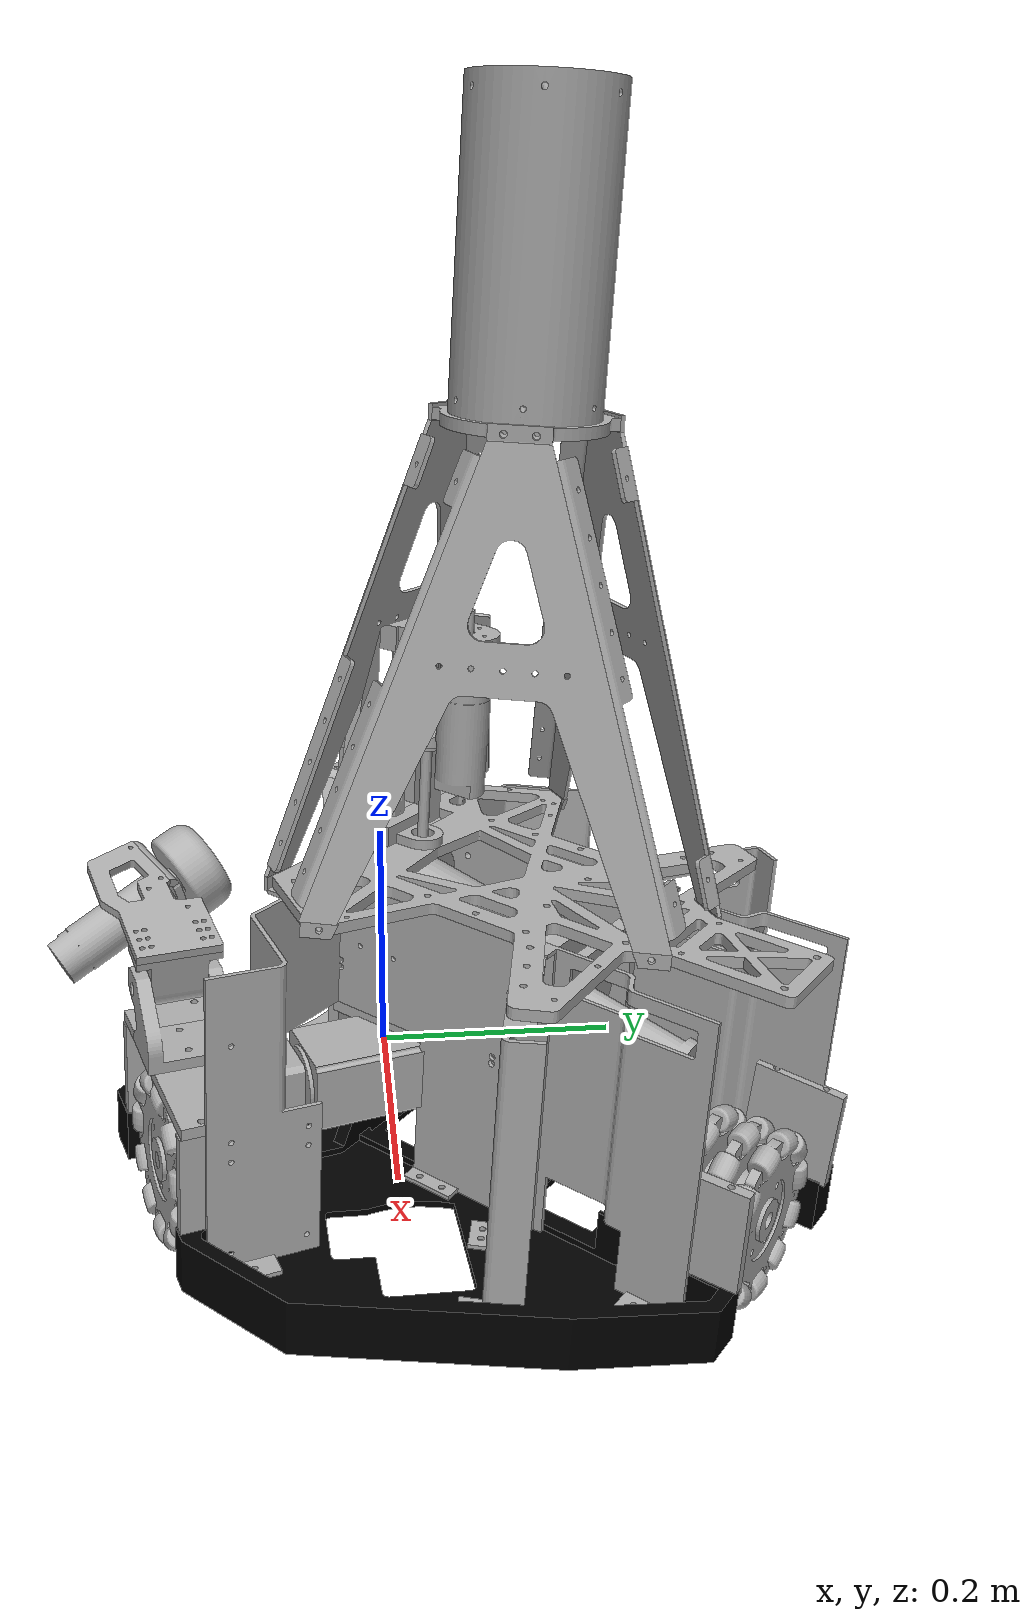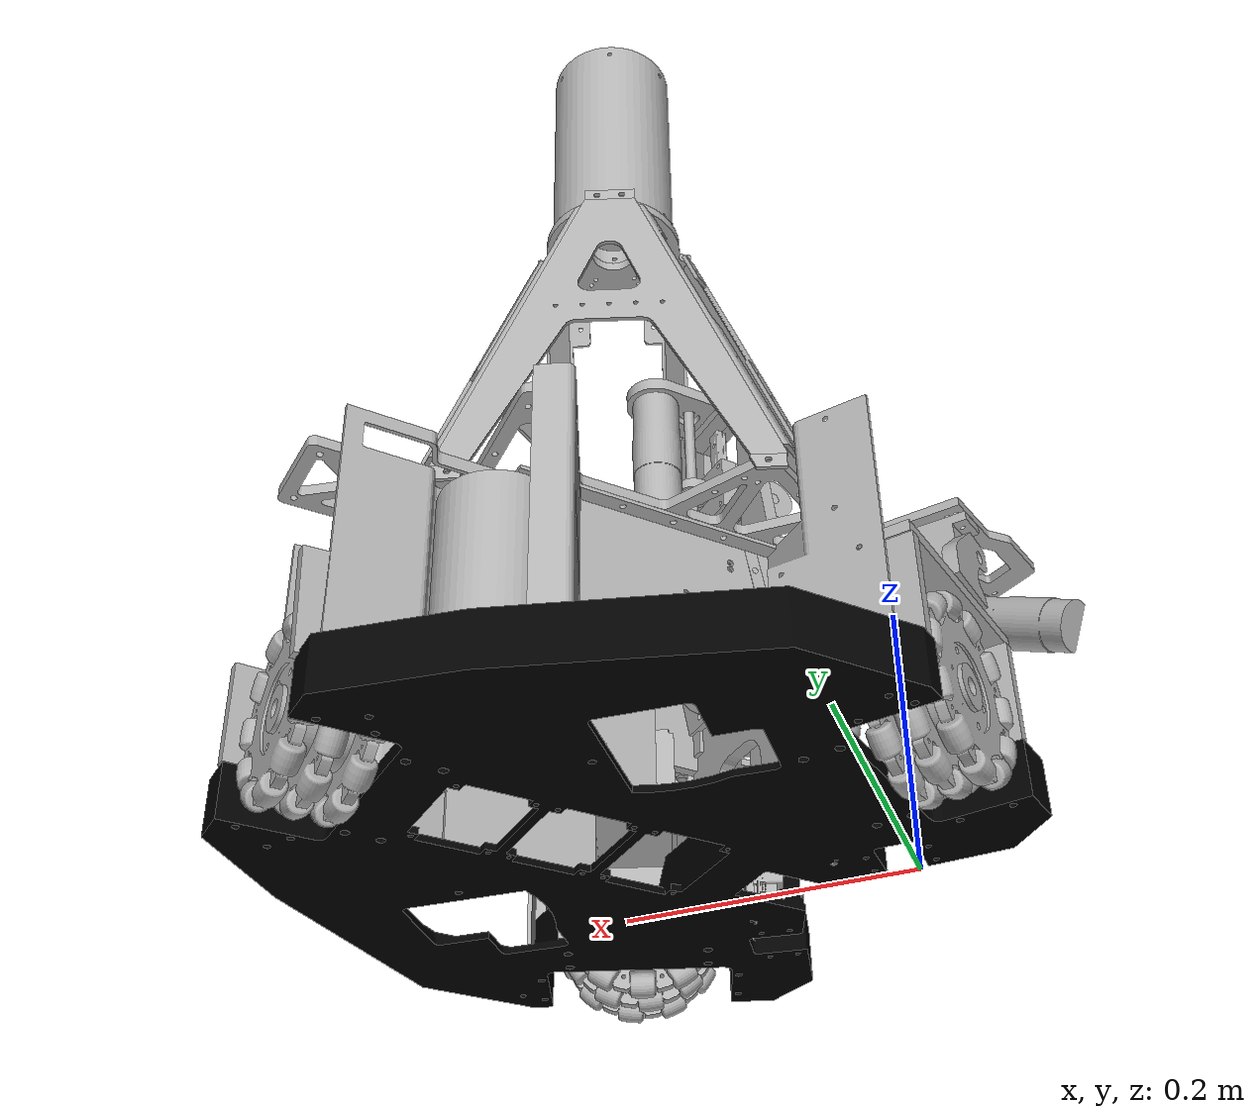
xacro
<?xml version="1.0" ?>
<robot name="iris_robot" xmlns:xacro="http://www.ros.org/wiki/xacro">

<xacro:include filename="$(find iris_robot_description)/urdf/materials.xacro" />
<xacro:include filename="$(find iris_robot_description)/urdf/iris_robot.trans" />
<xacro:include filename="$(find iris_robot_description)/urdf/iris_robot.gazebo" />
<link name="base_link">
  <inertial>
    <origin xyz="0.1831445962056383 0.07239617157428578 0.027463824756232526" rpy="0 0 0"/>
    <mass value="3.7613399363810003"/>
    <inertia ixx="0.074761" iyy="0.07222" izz="0.145535" ixy="0.006375" iyz="0.003562" ixz="3.1e-05"/>
  </inertial>
  <visual>
    <origin xyz="0 0 0" rpy="0 0 0"/>
    <geometry>
      <mesh filename="package://iris_robot_description/meshes/base_link.stl" scale="0.001 0.001 0.001"/>
    </geometry>
    <material name="black"/>
  </visual>
  <collision>
    <origin xyz="0 0 0" rpy="0 0 0"/>
    <geometry>
      <mesh filename="package://iris_robot_description/meshes/base_link.stl" scale="0.001 0.001 0.001"/>
    </geometry>
  </collision>
</link>

<link name="left_motor_bracket_1">
  <inertial>
    <origin xyz="-0.05169784408900585 -0.0009995867993597696 0.04948899961332788" rpy="0 0 0"/>
    <mass value="0.47321750244262606"/>
    <inertia ixx="0.000634" iyy="0.000857" izz="0.000382" ixy="-9e-05" iyz="0.0" ixz="-4e-06"/>
  </inertial>
  <visual>
    <origin xyz="-0.281529 0.091983 -0.03246" rpy="0 0 0"/>
    <geometry>
      <mesh filename="package://iris_robot_description/meshes/left_motor_bracket_1.stl" scale="0.001 0.001 0.001"/>
    </geometry>
    <material name="silver"/>
  </visual>
  <collision>
    <origin xyz="-0.281529 0.091983 -0.03246" rpy="0 0 0"/>
    <geometry>
      <mesh filename="package://iris_robot_description/meshes/left_motor_bracket_1.stl" scale="0.001 0.001 0.001"/>
    </geometry>
  </collision>
</link>

<link name="left_motor_1">
  <inertial>
    <origin xyz="-0.020854824190523702 0.05897416717439771 -0.0028578883066602556" rpy="0 0 0"/>
    <mass value="0.3401593265595349"/>
    <inertia ixx="0.000387" iyy="0.000201" izz="0.000434" ixy="7.5e-05" iyz="1.1e-05" ixz="-4e-06"/>
  </inertial>
  <visual>
    <origin xyz="-0.225736 0.079934 -0.10759" rpy="0 0 0"/>
    <geometry>
      <mesh filename="package://iris_robot_description/meshes/left_motor_1.stl" scale="0.001 0.001 0.001"/>
    </geometry>
    <material name="silver"/>
  </visual>
  <collision>
    <origin xyz="-0.225736 0.079934 -0.10759" rpy="0 0 0"/>
    <geometry>
      <mesh filename="package://iris_robot_description/meshes/left_motor_1.stl" scale="0.001 0.001 0.001"/>
    </geometry>
  </collision>
</link>

<link name="left_motor_ash_1">
  <inertial>
    <origin xyz="0.01604851559157805 -0.04538283527782078 0.002199674276821953" rpy="0 0 0"/>
    <mass value="0.08025811044162247"/>
    <inertia ixx="5.8e-05" iyy="9e-06" izz="6.4e-05" ixy="2e-05" iyz="3e-06" ixz="-1e-06"/>
  </inertial>
  <visual>
    <origin xyz="-0.224641 0.079103 -0.067002" rpy="0 0 0"/>
    <geometry>
      <mesh filename="package://iris_robot_description/meshes/left_motor_ash_1.stl" scale="0.001 0.001 0.001"/>
    </geometry>
    <material name="silver"/>
  </visual>
  <collision>
    <origin xyz="-0.224641 0.079103 -0.067002" rpy="0 0 0"/>
    <geometry>
      <mesh filename="package://iris_robot_description/meshes/left_motor_ash_1.stl" scale="0.001 0.001 0.001"/>
    </geometry>
  </collision>
</link>

<link name="left_motor_bracket_cover_1">
  <inertial>
    <origin xyz="-0.024381572659628287 -0.013054468112319514 -0.02473601529808811" rpy="0 0 0"/>
    <mass value="0.0769306560962844"/>
    <inertia ixx="3.3e-05" iyy="5.6e-05" izz="3.1e-05" ixy="-9e-06" iyz="-1e-06" ixz="0.0"/>
  </inertial>
  <visual>
    <origin xyz="-0.261697 0.101808 -0.094937" rpy="0 0 0"/>
    <geometry>
      <mesh filename="package://iris_robot_description/meshes/left_motor_bracket_cover_1.stl" scale="0.001 0.001 0.001"/>
    </geometry>
    <material name="silver"/>
  </visual>
  <collision>
    <origin xyz="-0.261697 0.101808 -0.094937" rpy="0 0 0"/>
    <geometry>
      <mesh filename="package://iris_robot_description/meshes/left_motor_bracket_cover_1.stl" scale="0.001 0.001 0.001"/>
    </geometry>
  </collision>
</link>

<link name="left_ash_to_omni_connector_front_1">
  <inertial>
    <origin xyz="-0.006617236538144222 0.01871226178128013 -0.0009064609879057689" rpy="0 0 0"/>
    <mass value="0.1791480879958417"/>
    <inertia ixx="5.8e-05" iyy="6.4e-05" izz="5.8e-05" ixy="-2e-06" iyz="-0.0" ixz="0.0"/>
  </inertial>
  <visual>
    <origin xyz="-0.257113 0.170929 -0.071452" rpy="0 0 0"/>
    <geometry>
      <mesh filename="package://iris_robot_description/meshes/left_ash_to_omni_connector_front_1.stl" scale="0.001 0.001 0.001"/>
    </geometry>
    <material name="silver"/>
  </visual>
  <collision>
    <origin xyz="-0.257113 0.170929 -0.071452" rpy="0 0 0"/>
    <geometry>
      <mesh filename="package://iris_robot_description/meshes/left_ash_to_omni_connector_front_1.stl" scale="0.001 0.001 0.001"/>
    </geometry>
  </collision>
</link>

<link name="front_right_omni_1">
  <inertial>
    <origin xyz="-0.01942590182350401 -0.008966780202215252 -0.010418035771954784" rpy="0 0 0"/>
    <mass value="0.23500963441195055"/>
    <inertia ixx="0.000307" iyy="0.000518" izz="0.000278" ixy="-8.5e-05" iyz="-1.2e-05" ixz="4e-06"/>
  </inertial>
  <visual>
    <origin xyz="-0.27504 0.157724 -0.081665" rpy="0 0 0"/>
    <geometry>
      <mesh filename="package://iris_robot_description/meshes/front_right_omni_1.stl" scale="0.001 0.001 0.001"/>
    </geometry>
    <material name="silver"/>
  </visual>
  <collision>
    <origin xyz="-0.27504 0.157724 -0.081665" rpy="0 0 0"/>
    <geometry>
      <mesh filename="package://iris_robot_description/meshes/front_right_omni_1.stl" scale="0.001 0.001 0.001"/>
    </geometry>
  </collision>
</link>

<link name="mid_right_omni_1">
  <inertial>
    <origin xyz="-0.01973886434902064 -0.0047501977858498134 0.013159920747479098" rpy="0 0 0"/>
    <mass value="0.2348808094813233"/>
    <inertia ixx="0.000307" iyy="0.000518" izz="0.000278" ixy="-8.5e-05" iyz="-1.2e-05" ixz="4e-06"/>
  </inertial>
  <visual>
    <origin xyz="-0.267934 0.142311 -0.057169" rpy="0 0 0"/>
    <geometry>
      <mesh filename="package://iris_robot_description/meshes/mid_right_omni_1.stl" scale="0.001 0.001 0.001"/>
    </geometry>
    <material name="silver"/>
  </visual>
  <collision>
    <origin xyz="-0.267934 0.142311 -0.057169" rpy="0 0 0"/>
    <geometry>
      <mesh filename="package://iris_robot_description/meshes/mid_right_omni_1.stl" scale="0.001 0.001 0.001"/>
    </geometry>
  </collision>
</link>

<link name="left_ash_to_omni_connector_rear_1">
  <inertial>
    <origin xyz="-0.020120484439436953 0.0032920238285845393 0.017557937881550634" rpy="0 0 0"/>
    <mass value="0.09595762654106495"/>
    <inertia ixx="3.2e-05" iyy="5.1e-05" izz="2.9e-05" ixy="-8e-06" iyz="-1e-06" ixz="0.0"/>
  </inertial>
  <visual>
    <origin xyz="-0.262736 0.141195 -0.05241" rpy="0 0 0"/>
    <geometry>
      <mesh filename="package://iris_robot_description/meshes/left_ash_to_omni_connector_rear_1.stl" scale="0.001 0.001 0.001"/>
    </geometry>
    <material name="silver"/>
  </visual>
  <collision>
    <origin xyz="-0.262736 0.141195 -0.05241" rpy="0 0 0"/>
    <geometry>
      <mesh filename="package://iris_robot_description/meshes/left_ash_to_omni_connector_rear_1.stl" scale="0.001 0.001 0.001"/>
    </geometry>
  </collision>
</link>

<link name="rear_right_omni_1">
  <inertial>
    <origin xyz="-0.017440703587482093 -0.0038125251946335426 0.015735515057858036" rpy="0 0 0"/>
    <mass value="0.23500963441194936"/>
    <inertia ixx="0.000307" iyy="0.000518" izz="0.000278" ixy="-8.5e-05" iyz="-1.2e-05" ixz="4e-06"/>
  </inertial>
  <visual>
    <origin xyz="-0.256983 0.123951 -0.05583" rpy="0 0 0"/>
    <geometry>
      <mesh filename="package://iris_robot_description/meshes/rear_right_omni_1.stl" scale="0.001 0.001 0.001"/>
    </geometry>
    <material name="silver"/>
  </visual>
  <collision>
    <origin xyz="-0.256983 0.123951 -0.05583" rpy="0 0 0"/>
    <geometry>
      <mesh filename="package://iris_robot_description/meshes/rear_right_omni_1.stl" scale="0.001 0.001 0.001"/>
    </geometry>
  </collision>
</link>

<link name="rear_motor_bracket_1">
  <inertial>
    <origin xyz="-0.0313879720509227 0.04246971448699596 0.04729783577769485" rpy="0 0 0"/>
    <mass value="0.47321750244279526"/>
    <inertia ixx="0.000723" iyy="0.000764" izz="0.000386" ixy="0.00014" iyz="-3.8e-05" ixz="-2.4e-05"/>
  </inertial>
  <visual>
    <origin xyz="-0.312414 -0.139178 -0.020992" rpy="0 0 0"/>
    <geometry>
      <mesh filename="package://iris_robot_description/meshes/rear_motor_bracket_1.stl" scale="0.001 0.001 0.001"/>
    </geometry>
    <material name="silver"/>
  </visual>
  <collision>
    <origin xyz="-0.312414 -0.139178 -0.020992" rpy="0 0 0"/>
    <geometry>
      <mesh filename="package://iris_robot_description/meshes/rear_motor_bracket_1.stl" scale="0.001 0.001 0.001"/>
    </geometry>
  </collision>
</link>

<link name="rear_motor_bracket_cover_1">
  <inertial>
    <origin xyz="-0.01849751708285191 0.018509245453901563 -0.026305690640984522" rpy="0 0 0"/>
    <mass value="0.07693065609628418"/>
    <inertia ixx="4.2e-05" iyy="4.7e-05" izz="3.1e-05" ixy="1.5e-05" iyz="-1e-06" ixz="-1e-06"/>
  </inertial>
  <visual>
    <origin xyz="-0.314161 -0.179631 -0.080939" rpy="0 0 0"/>
    <geometry>
      <mesh filename="package://iris_robot_description/meshes/rear_motor_bracket_cover_1.stl" scale="0.001 0.001 0.001"/>
    </geometry>
    <material name="silver"/>
  </visual>
  <collision>
    <origin xyz="-0.314161 -0.179631 -0.080939" rpy="0 0 0"/>
    <geometry>
      <mesh filename="package://iris_robot_description/meshes/rear_motor_bracket_cover_1.stl" scale="0.001 0.001 0.001"/>
    </geometry>
  </collision>
</link>

<link name="rear_motor_1">
  <inertial>
    <origin xyz="-0.034205608125721654 -0.03993055228243836 0.002048985812911089" rpy="0 0 0"/>
    <mass value="0.3401593265595337"/>
    <inertia ixx="0.000312" iyy="0.000276" izz="0.000435" ixy="-0.000118" iyz="8e-06" ixz="6e-06"/>
  </inertial>
  <visual>
    <origin xyz="-0.272973 -0.173467 -0.094987" rpy="0 0 0"/>
    <geometry>
      <mesh filename="package://iris_robot_description/meshes/rear_motor_1.stl" scale="0.001 0.001 0.001"/>
    </geometry>
    <material name="silver"/>
  </visual>
  <collision>
    <origin xyz="-0.272973 -0.173467 -0.094987" rpy="0 0 0"/>
    <geometry>
      <mesh filename="package://iris_robot_description/meshes/rear_motor_1.stl" scale="0.001 0.001 0.001"/>
    </geometry>
  </collision>
</link>

<link name="rear_motor_ash_1">
  <inertial>
    <origin xyz="0.03132573186382048 0.03656822992352057 -0.001876824879557197" rpy="0 0 0"/>
    <mass value="0.0802581104416225"/>
    <inertia ixx="3.8e-05" iyy="2.8e-05" izz="6.4e-05" ixy="-3.1e-05" iyz="2e-06" ixz="2e-06"/>
  </inertial>
  <visual>
    <origin xyz="-0.270927 -0.169196 -0.054653" rpy="0 0 0"/>
    <geometry>
      <mesh filename="package://iris_robot_description/meshes/rear_motor_ash_1.stl" scale="0.001 0.001 0.001"/>
    </geometry>
    <material name="silver"/>
  </visual>
  <collision>
    <origin xyz="-0.270927 -0.169196 -0.054653" rpy="0 0 0"/>
    <geometry>
      <mesh filename="package://iris_robot_description/meshes/rear_motor_ash_1.stl" scale="0.001 0.001 0.001"/>
    </geometry>
  </collision>
</link>

<link name="rear_ash_to_omni_connector_rear_1">
  <inertial>
    <origin xyz="-0.012916225431386319 -0.015077263370777416 0.0007734616035909858" rpy="0 0 0"/>
    <mass value="0.17914808799583984"/>
    <inertia ixx="6.1e-05" iyy="6.2e-05" izz="5.8e-05" ixy="3e-06" iyz="-0.0" ixz="-0.0"/>
  </inertial>
  <visual>
    <origin xyz="-0.33431 -0.243186 -0.050856" rpy="0 0 0"/>
    <geometry>
      <mesh filename="package://iris_robot_description/meshes/rear_ash_to_omni_connector_rear_1.stl" scale="0.001 0.001 0.001"/>
    </geometry>
    <material name="silver"/>
  </visual>
  <collision>
    <origin xyz="-0.33431 -0.243186 -0.050856" rpy="0 0 0"/>
    <geometry>
      <mesh filename="package://iris_robot_description/meshes/rear_ash_to_omni_connector_rear_1.stl" scale="0.001 0.001 0.001"/>
    </geometry>
  </collision>
</link>

<link name="front_rear_omni_1">
  <inertial>
    <origin xyz="-0.005150629148113484 0.005227369059485898 -0.022637061272269964" rpy="0 0 0"/>
    <mass value="0.23500963441722925"/>
    <inertia ixx="0.000392" iyy="0.000433" izz="0.000277" ixy="0.000134" iyz="-8e-06" ixz="-7e-06"/>
  </inertial>
  <visual>
    <origin xyz="-0.336535 -0.234544 -0.073668" rpy="0 0 0"/>
    <geometry>
      <mesh filename="package://iris_robot_description/meshes/front_rear_omni_1.stl" scale="0.001 0.001 0.001"/>
    </geometry>
    <material name="silver"/>
  </visual>
  <collision>
    <origin xyz="-0.336535 -0.234544 -0.073668" rpy="0 0 0"/>
    <geometry>
      <mesh filename="package://iris_robot_description/meshes/front_rear_omni_1.stl" scale="0.001 0.001 0.001"/>
    </geometry>
  </collision>
</link>

<link name="mid_rear_omni_1">
  <inertial>
    <origin xyz="-0.0009652793713543217 -0.0011462959078379353 6.143452858713844e-05" rpy="0 0 0"/>
    <mass value="0.23488080945950318"/>
    <inertia ixx="0.000392" iyy="0.000433" izz="0.000277" ixy="0.000134" iyz="-8e-06" ixz="-7e-06"/>
  </inertial>
  <visual>
    <origin xyz="-0.318708 -0.224973 -0.05179" rpy="0 0 0"/>
    <geometry>
      <mesh filename="package://iris_robot_description/meshes/mid_rear_omni_1.stl" scale="0.001 0.001 0.001"/>
    </geometry>
    <material name="silver"/>
  </visual>
  <collision>
    <origin xyz="-0.318708 -0.224973 -0.05179" rpy="0 0 0"/>
    <geometry>
      <mesh filename="package://iris_robot_description/meshes/mid_rear_omni_1.stl" scale="0.001 0.001 0.001"/>
    </geometry>
  </collision>
</link>

<link name="rear_ash_to_omni_connector_2_rear_1">
  <inertial>
    <origin xyz="-0.005829169498870246 -0.006848254205235438 0.0003582234948567159" rpy="0 0 0"/>
    <mass value="0.09595762654117547"/>
    <inertia ixx="3.9e-05" iyy="4.3e-05" izz="2.9e-05" ixy="1.2e-05" iyz="-1e-06" ixz="-1e-06"/>
  </inertial>
  <visual>
    <origin xyz="-0.315458 -0.221179 -0.051985" rpy="0 0 0"/>
    <geometry>
      <mesh filename="package://iris_robot_description/meshes/rear_ash_to_omni_connector_2_rear_1.stl" scale="0.001 0.001 0.001"/>
    </geometry>
    <material name="silver"/>
  </visual>
  <collision>
    <origin xyz="-0.315458 -0.221179 -0.051985" rpy="0 0 0"/>
    <geometry>
      <mesh filename="package://iris_robot_description/meshes/rear_ash_to_omni_connector_2_rear_1.stl" scale="0.001 0.001 0.001"/>
    </geometry>
  </collision>
</link>

<link name="rear_rear_omni_1">
  <inertial>
    <origin xyz="-0.0009749113735100234 -0.001137987008417829 5.8521988757449794e-05" rpy="0 0 0"/>
    <mass value="0.23500963441722744"/>
    <inertia ixx="0.000392" iyy="0.000433" izz="0.000277" ixy="0.000134" iyz="-8e-06" ixz="-7e-06"/>
  </inertial>
  <visual>
    <origin xyz="-0.303756 -0.207519 -0.052686" rpy="0 0 0"/>
    <geometry>
      <mesh filename="package://iris_robot_description/meshes/rear_rear_omni_1.stl" scale="0.001 0.001 0.001"/>
    </geometry>
    <material name="silver"/>
  </visual>
  <collision>
    <origin xyz="-0.303756 -0.207519 -0.052686" rpy="0 0 0"/>
    <geometry>
      <mesh filename="package://iris_robot_description/meshes/rear_rear_omni_1.stl" scale="0.001 0.001 0.001"/>
    </geometry>
  </collision>
</link>

<link name="right_motor_bracket_1">
  <inertial>
    <origin xyz="-0.0005443372892179228 0.05334574603205128 0.046688349355051714" rpy="0 0 0"/>
    <mass value="0.4732175024428434"/>
    <inertia ixx="0.000878" iyy="0.000611" izz="0.000384" ixy="-5e-05" iyz="-1.6e-05" ixz="2.5e-05"/>
  </inertial>
  <visual>
    <origin xyz="-0.017841 -0.035302 -0.026809" rpy="0 0 0"/>
    <geometry>
      <mesh filename="package://iris_robot_description/meshes/right_motor_bracket_1.stl" scale="0.001 0.001 0.001"/>
    </geometry>
    <material name="silver"/>
  </visual>
  <collision>
    <origin xyz="-0.017841 -0.035302 -0.026809" rpy="0 0 0"/>
    <geometry>
      <mesh filename="package://iris_robot_description/meshes/right_motor_bracket_1.stl" scale="0.001 0.001 0.001"/>
    </geometry>
  </collision>
</link>

<link name="right_motor_1">
  <inertial>
    <origin xyz="0.051756019166527736 -0.009651522077189181 0.000337591836623935" rpy="0 0 0"/>
    <mass value="0.33990296538909626"/>
    <inertia ixx="0.000182" iyy="0.000405" izz="0.000434" ixy="4.3e-05" iyz="2e-06" ixz="-2e-06"/>
  </inertial>
  <visual>
    <origin xyz="-0.02963 -0.087656 -0.099792" rpy="0 0 0"/>
    <geometry>
      <mesh filename="package://iris_robot_description/meshes/right_motor_1.stl" scale="0.001 0.001 0.001"/>
    </geometry>
    <material name="silver"/>
  </visual>
  <collision>
    <origin xyz="-0.02963 -0.087656 -0.099792" rpy="0 0 0"/>
    <geometry>
      <mesh filename="package://iris_robot_description/meshes/right_motor_1.stl" scale="0.001 0.001 0.001"/>
    </geometry>
  </collision>
</link>

<link name="right_motor_ash_1">
  <inertial>
    <origin xyz="-0.04737266627589722 0.008816300693298904 -0.0003226520322519577" rpy="0 0 0"/>
    <mass value="0.08025811044162175"/>
    <inertia ixx="4e-06" iyy="6.2e-05" izz="6.4e-05" ixy="1.1e-05" iyz="0.0" ixz="-0.0"/>
  </inertial>
  <visual>
    <origin xyz="-0.032484 -0.085113 -0.059361" rpy="0 0 0"/>
    <geometry>
      <mesh filename="package://iris_robot_description/meshes/right_motor_ash_1.stl" scale="0.001 0.001 0.001"/>
    </geometry>
    <material name="silver"/>
  </visual>
  <collision>
    <origin xyz="-0.032484 -0.085113 -0.059361" rpy="0 0 0"/>
    <geometry>
      <mesh filename="package://iris_robot_description/meshes/right_motor_ash_1.stl" scale="0.001 0.001 0.001"/>
    </geometry>
  </collision>
</link>

<link name="right_ash_to_omni_connector_1">
  <inertial>
    <origin xyz="0.01953262417806799 -0.0036346247980936913 0.00013316194129961434" rpy="0 0 0"/>
    <mass value="0.1791480879958664"/>
    <inertia ixx="6.4e-05" iyy="5.8e-05" izz="5.8e-05" ixy="-1e-06" iyz="-0.0" ixz="0.0"/>
  </inertial>
  <visual>
    <origin xyz="0.063368 -0.102951 -0.058708" rpy="0 0 0"/>
    <geometry>
      <mesh filename="package://iris_robot_description/meshes/right_ash_to_omni_connector_1.stl" scale="0.001 0.001 0.001"/>
    </geometry>
    <material name="silver"/>
  </visual>
  <collision>
    <origin xyz="0.063368 -0.102951 -0.058708" rpy="0 0 0"/>
    <geometry>
      <mesh filename="package://iris_robot_description/meshes/right_ash_to_omni_connector_1.stl" scale="0.001 0.001 0.001"/>
    </geometry>
  </collision>
</link>

<link name="right_front_right_omni_1">
  <inertial>
    <origin xyz="-0.0031660035523448163 -0.009601861221357408 -0.021542758577139748" rpy="0 0 0"/>
    <mass value="0.2350096344278615"/>
    <inertia ixx="0.000539" iyy="0.000286" izz="0.000277" ixy="-4.9e-05" iyz="-0.0" ixz="2e-06"/>
  </inertial>
  <visual>
    <origin xyz="0.055778 -0.11173 -0.080281" rpy="0 0 0"/>
    <geometry>
      <mesh filename="package://iris_robot_description/meshes/right_front_right_omni_1.stl" scale="0.001 0.001 0.001"/>
    </geometry>
    <material name="silver"/>
  </visual>
  <collision>
    <origin xyz="0.055778 -0.11173 -0.080281" rpy="0 0 0"/>
    <geometry>
      <mesh filename="package://iris_robot_description/meshes/right_front_right_omni_1.stl" scale="0.001 0.001 0.001"/>
    </geometry>
  </collision>
</link>

<link name="right_mid_right_omni_1">
  <inertial>
    <origin xyz="0.005866036847804797 0.02339406406527389 0.0019190173778923028" rpy="0 0 0"/>
    <mass value="0.2348808094962352"/>
    <inertia ixx="0.000539" iyy="0.000286" izz="0.000277" ixy="-4.9e-05" iyz="-0.0" ixz="2e-06"/>
  </inertial>
  <visual>
    <origin xyz="0.044088 -0.075299 -0.056779" rpy="0 0 0"/>
    <geometry>
      <mesh filename="package://iris_robot_description/meshes/right_mid_right_omni_1.stl" scale="0.001 0.001 0.001"/>
    </geometry>
    <material name="silver"/>
  </visual>
  <collision>
    <origin xyz="0.044088 -0.075299 -0.056779" rpy="0 0 0"/>
    <geometry>
      <mesh filename="package://iris_robot_description/meshes/right_mid_right_omni_1.stl" scale="0.001 0.001 0.001"/>
    </geometry>
  </collision>
</link>

<link name="right_ash_to_omni_connector_2_1">
  <inertial>
    <origin xyz="0.007883157122336094 -0.007671688208869806 -0.022875849796621966" rpy="0 0 0"/>
    <mass value="0.09595762654107597"/>
    <inertia ixx="5.3e-05" iyy="3e-05" izz="2.9e-05" ixy="-4e-06" iyz="-0.0" ixz="0.0"/>
  </inertial>
  <visual>
    <origin xyz="0.036153 -0.10247 -0.082099" rpy="0 0 0"/>
    <geometry>
      <mesh filename="package://iris_robot_description/meshes/right_ash_to_omni_connector_2_1.stl" scale="0.001 0.001 0.001"/>
    </geometry>
    <material name="silver"/>
  </visual>
  <collision>
    <origin xyz="0.036153 -0.10247 -0.082099" rpy="0 0 0"/>
    <geometry>
      <mesh filename="package://iris_robot_description/meshes/right_ash_to_omni_connector_2_1.stl" scale="0.001 0.001 0.001"/>
    </geometry>
  </collision>
</link>

<link name="right_rear_right_omni_1">
  <inertial>
    <origin xyz="0.0014745810251055001 -0.0002745028611105399 1.035778614158489e-05" rpy="0 0 0"/>
    <mass value="0.23500963442786377"/>
    <inertia ixx="0.000539" iyy="0.000286" izz="0.000277" ixy="-4.9e-05" iyz="-0.0" ixz="2e-06"/>
  </inertial>
  <visual>
    <origin xyz="0.019427 -0.093124 -0.059274" rpy="0 0 0"/>
    <geometry>
      <mesh filename="package://iris_robot_description/meshes/right_rear_right_omni_1.stl" scale="0.001 0.001 0.001"/>
    </geometry>
    <material name="silver"/>
  </visual>
  <collision>
    <origin xyz="0.019427 -0.093124 -0.059274" rpy="0 0 0"/>
    <geometry>
      <mesh filename="package://iris_robot_description/meshes/right_rear_right_omni_1.stl" scale="0.001 0.001 0.001"/>
    </geometry>
  </collision>
</link>

<link name="back_stand_1">
  <inertial>
    <origin xyz="0.013983814812666473 0.019653554003608853 0.034669826850251495" rpy="0 0 0"/>
    <mass value="0.10115982495882724"/>
    <inertia ixx="6.5e-05" iyy="5.9e-05" izz="3.7e-05" ixy="-1.8e-05" iyz="-2e-06" ixz="2e-06"/>
  </inertial>
  <visual>
    <origin xyz="-0.25288 -0.259286 -0.045248" rpy="0 0 0"/>
    <geometry>
      <mesh filename="package://iris_robot_description/meshes/back_stand_1.stl" scale="0.001 0.001 0.001"/>
    </geometry>
    <material name="silver"/>
  </visual>
  <collision>
    <origin xyz="-0.25288 -0.259286 -0.045248" rpy="0 0 0"/>
    <geometry>
      <mesh filename="package://iris_robot_description/meshes/back_stand_1.stl" scale="0.001 0.001 0.001"/>
    </geometry>
  </collision>
</link>

<link name="back_stand_2_1">
  <inertial>
    <origin xyz="0.011794056221320348 0.016423571731278314 0.03570671005691215" rpy="0 0 0"/>
    <mass value="0.10115982495882658"/>
    <inertia ixx="6.6e-05" iyy="5.8e-05" izz="3.7e-05" ixy="-1.7e-05" iyz="-1e-06" ixz="1e-06"/>
  </inertial>
  <visual>
    <origin xyz="-0.36306 -0.165126 -0.04963" rpy="0 0 0"/>
    <geometry>
      <mesh filename="package://iris_robot_description/meshes/back_stand_2_1.stl" scale="0.001 0.001 0.001"/>
    </geometry>
    <material name="silver"/>
  </visual>
  <collision>
    <origin xyz="-0.36306 -0.165126 -0.04963" rpy="0 0 0"/>
    <geometry>
      <mesh filename="package://iris_robot_description/meshes/back_stand_2_1.stl" scale="0.001 0.001 0.001"/>
    </geometry>
  </collision>
</link>

<link name="left_stand_1">
  <inertial>
    <origin xyz="-0.006158293946634363 0.019456201041546273 0.03560006609933064" rpy="0 0 0"/>
    <mass value="0.10115982495882687"/>
    <inertia ixx="7.6e-05" iyy="4.8e-05" izz="3.7e-05" ixy="1.1e-05" iyz="-1e-06" ixz="-1e-06"/>
  </inertial>
  <visual>
    <origin xyz="-0.322128 0.137651 -0.064652" rpy="0 0 0"/>
    <geometry>
      <mesh filename="package://iris_robot_description/meshes/left_stand_1.stl" scale="0.001 0.001 0.001"/>
    </geometry>
    <material name="silver"/>
  </visual>
  <collision>
    <origin xyz="-0.322128 0.137651 -0.064652" rpy="0 0 0"/>
    <geometry>
      <mesh filename="package://iris_robot_description/meshes/left_stand_1.stl" scale="0.001 0.001 0.001"/>
    </geometry>
  </collision>
</link>

<link name="left_stand_2_1">
  <inertial>
    <origin xyz="-0.006157924398742548 0.019455642321557526 0.035599820100527826" rpy="0 0 0"/>
    <mass value="0.10115982495882704"/>
    <inertia ixx="7.6e-05" iyy="4.8e-05" izz="3.7e-05" ixy="1.1e-05" iyz="-1e-06" ixz="-1e-06"/>
  </inertial>
  <visual>
    <origin xyz="-0.185405 0.185865 -0.067352" rpy="0 0 0"/>
    <geometry>
      <mesh filename="package://iris_robot_description/meshes/left_stand_2_1.stl" scale="0.001 0.001 0.001"/>
    </geometry>
    <material name="silver"/>
  </visual>
  <collision>
    <origin xyz="-0.185405 0.185865 -0.067352" rpy="0 0 0"/>
    <geometry>
      <mesh filename="package://iris_robot_description/meshes/left_stand_2_1.stl" scale="0.001 0.001 0.001"/>
    </geometry>
  </collision>
</link>

<link name="right_stand_1">
  <inertial>
    <origin xyz="0.018513139831437455 -0.0016644422709958528 0.03658248176043292" rpy="0 0 0"/>
    <mass value="0.10115982495882687"/>
    <inertia ixx="4.6e-05" iyy="7.9e-05" izz="3.7e-05" ixy="6e-06" iyz="-2e-06" ixz="-0.0"/>
  </inertial>
  <visual>
    <origin xyz="0.040278 -0.172059 -0.050241" rpy="0 0 0"/>
    <geometry>
      <mesh filename="package://iris_robot_description/meshes/right_stand_1.stl" scale="0.001 0.001 0.001"/>
    </geometry>
    <material name="silver"/>
  </visual>
  <collision>
    <origin xyz="0.040278 -0.172059 -0.050241" rpy="0 0 0"/>
    <geometry>
      <mesh filename="package://iris_robot_description/meshes/right_stand_1.stl" scale="0.001 0.001 0.001"/>
    </geometry>
  </collision>
</link>

<link name="right_stand_2_1">
  <inertial>
    <origin xyz="0.018525966390376014 -0.001598412409221272 0.036579754664850424" rpy="0 0 0"/>
    <mass value="0.10115982495882693"/>
    <inertia ixx="4.5e-05" iyy="7.9e-05" izz="3.7e-05" ixy="6e-06" iyz="-2e-06" ixz="-0.0"/>
  </inertial>
  <visual>
    <origin xyz="0.066819 -0.029698 -0.057467" rpy="0 0 0"/>
    <geometry>
      <mesh filename="package://iris_robot_description/meshes/right_stand_2_1.stl" scale="0.001 0.001 0.001"/>
    </geometry>
    <material name="silver"/>
  </visual>
  <collision>
    <origin xyz="0.066819 -0.029698 -0.057467" rpy="0 0 0"/>
    <geometry>
      <mesh filename="package://iris_robot_description/meshes/right_stand_2_1.stl" scale="0.001 0.001 0.001"/>
    </geometry>
  </collision>
</link>

<link name="right_dribble_base_1">
  <inertial>
    <origin xyz="-0.004121958012669343 0.0747357974788617 0.0003306354487902785" rpy="0 0 0"/>
    <mass value="0.08008274771247241"/>
    <inertia ixx="0.000154" iyy="3.4e-05" izz="0.000187" ixy="-2.3e-05" iyz="8e-06" ixz="1e-06"/>
  </inertial>
  <visual>
    <origin xyz="0.029767 -0.026501 -0.130626" rpy="0 0 0"/>
    <geometry>
      <mesh filename="package://iris_robot_description/meshes/right_dribble_base_1.stl" scale="0.001 0.001 0.001"/>
    </geometry>
    <material name="silver"/>
  </visual>
  <collision>
    <origin xyz="0.029767 -0.026501 -0.130626" rpy="0 0 0"/>
    <geometry>
      <mesh filename="package://iris_robot_description/meshes/right_dribble_base_1.stl" scale="0.001 0.001 0.001"/>
    </geometry>
  </collision>
</link>

<link name="left_dribble__base_1">
  <inertial>
    <origin xyz="0.0743778991883289 0.007650406434733498 0.0034517069373495857" rpy="0 0 0"/>
    <mass value="0.08008274771247227"/>
    <inertia ixx="4.4e-05" iyy="0.000144" izz="0.000187" ixy="-4.1e-05" iyz="2e-06" ixz="2e-06"/>
  </inertial>
  <visual>
    <origin xyz="-0.173089 0.146953 -0.138552" rpy="0 0 0"/>
    <geometry>
      <mesh filename="package://iris_robot_description/meshes/left_dribble__base_1.stl" scale="0.001 0.001 0.001"/>
    </geometry>
    <material name="silver"/>
  </visual>
  <collision>
    <origin xyz="-0.173089 0.146953 -0.138552" rpy="0 0 0"/>
    <geometry>
      <mesh filename="package://iris_robot_description/meshes/left_dribble__base_1.stl" scale="0.001 0.001 0.001"/>
    </geometry>
  </collision>
</link>

<link name="left_gp_stand_1">
  <inertial>
    <origin xyz="4.72215829349365e-05 0.000979437756659457 0.019877471276591487" rpy="0 0 0"/>
    <mass value="0.010745999999999084"/>
    <inertia ixx="2e-06" iyy="1e-06" izz="0.0" ixy="0.0" iyz="-0.0" ixz="-0.0"/>
  </inertial>
  <visual>
    <origin xyz="-0.135533 0.069101 -0.023667" rpy="0 0 0"/>
    <geometry>
      <mesh filename="package://iris_robot_description/meshes/left_gp_stand_1.stl" scale="0.001 0.001 0.001"/>
    </geometry>
    <material name="silver"/>
  </visual>
  <collision>
    <origin xyz="-0.135533 0.069101 -0.023667" rpy="0 0 0"/>
    <geometry>
      <mesh filename="package://iris_robot_description/meshes/left_gp_stand_1.stl" scale="0.001 0.001 0.001"/>
    </geometry>
  </collision>
</link>

<link name="right_gp_stand_1">
  <inertial>
    <origin xyz="4.739492682316604e-05 0.0009793803871059868 0.019877019410197556" rpy="0 0 0"/>
    <mass value="0.010746000000001104"/>
    <inertia ixx="1e-06" iyy="2e-06" izz="0.0" ixy="0.0" iyz="-0.0" ixz="-0.0"/>
  </inertial>
  <visual>
    <origin xyz="-0.05537 0.002406 -0.020569" rpy="0 0 0"/>
    <geometry>
      <mesh filename="package://iris_robot_description/meshes/right_gp_stand_1.stl" scale="0.001 0.001 0.001"/>
    </geometry>
    <material name="silver"/>
  </visual>
  <collision>
    <origin xyz="-0.05537 0.002406 -0.020569" rpy="0 0 0"/>
    <geometry>
      <mesh filename="package://iris_robot_description/meshes/right_gp_stand_1.stl" scale="0.001 0.001 0.001"/>
    </geometry>
  </collision>
</link>

<link name="left_gp_1">
  <inertial>
    <origin xyz="-0.008105547348915276 -0.006395082875981117 -0.0006003368504454085" rpy="0 0 0"/>
    <mass value="0.005571407726622197"/>
    <inertia ixx="1e-06" iyy="1e-06" izz="0.0" ixy="-0.0" iyz="-0.0" ixz="-0.0"/>
  </inertial>
  <visual>
    <origin xyz="-0.133222 0.068973 -0.04319" rpy="0 0 0"/>
    <geometry>
      <mesh filename="package://iris_robot_description/meshes/left_gp_1.stl" scale="0.001 0.001 0.001"/>
    </geometry>
    <material name="silver"/>
  </visual>
  <collision>
    <origin xyz="-0.133222 0.068973 -0.04319" rpy="0 0 0"/>
    <geometry>
      <mesh filename="package://iris_robot_description/meshes/left_gp_1.stl" scale="0.001 0.001 0.001"/>
    </geometry>
  </collision>
</link>

<link name="right_gp_1">
  <inertial>
    <origin xyz="0.0014526817858374133 -0.010231666153651599 -0.00043445137175977117" rpy="0 0 0"/>
    <mass value="0.005570925816354775"/>
    <inertia ixx="1e-06" iyy="1e-06" izz="0.0" ixy="-0.0" iyz="-0.0" ixz="-0.0"/>
  </inertial>
  <visual>
    <origin xyz="-0.054959 0.003901 -0.040167" rpy="0 0 0"/>
    <geometry>
      <mesh filename="package://iris_robot_description/meshes/right_gp_1.stl" scale="0.001 0.001 0.001"/>
    </geometry>
    <material name="silver"/>
  </visual>
  <collision>
    <origin xyz="-0.054959 0.003901 -0.040167" rpy="0 0 0"/>
    <geometry>
      <mesh filename="package://iris_robot_description/meshes/right_gp_1.stl" scale="0.001 0.001 0.001"/>
    </geometry>
  </collision>
</link>

<link name="right_free_wheel_holder_1">
  <inertial>
    <origin xyz="-0.001929854511457732 0.010805524489575684 0.015695746707999857" rpy="0 0 0"/>
    <mass value="0.006353274364026673"/>
    <inertia ixx="1e-06" iyy="1e-06" izz="0.0" ixy="-0.0" iyz="-0.0" ixz="-0.0"/>
  </inertial>
  <visual>
    <origin xyz="-0.036172 0.024628 -0.059756" rpy="0 0 0"/>
    <geometry>
      <mesh filename="package://iris_robot_description/meshes/right_free_wheel_holder_1.stl" scale="0.001 0.001 0.001"/>
    </geometry>
    <material name="silver"/>
  </visual>
  <collision>
    <origin xyz="-0.036172 0.024628 -0.059756" rpy="0 0 0"/>
    <geometry>
      <mesh filename="package://iris_robot_description/meshes/right_free_wheel_holder_1.stl" scale="0.001 0.001 0.001"/>
    </geometry>
  </collision>
</link>

<link name="right_free_wheel_holder_2_1">
  <inertial>
    <origin xyz="0.0022146757042597687 0.009534362890779998 0.015330725540270151" rpy="0 0 0"/>
    <mass value="0.006353274364026674"/>
    <inertia ixx="1e-06" iyy="1e-06" izz="0.0" ixy="-0.0" iyz="-0.0" ixz="0.0"/>
  </inertial>
  <visual>
    <origin xyz="0.005326 0.024227 -0.059834" rpy="0 0 0"/>
    <geometry>
      <mesh filename="package://iris_robot_description/meshes/right_free_wheel_holder_2_1.stl" scale="0.001 0.001 0.001"/>
    </geometry>
    <material name="silver"/>
  </visual>
  <collision>
    <origin xyz="0.005326 0.024227 -0.059834" rpy="0 0 0"/>
    <geometry>
      <mesh filename="package://iris_robot_description/meshes/right_free_wheel_holder_2_1.stl" scale="0.001 0.001 0.001"/>
    </geometry>
  </collision>
</link>

<link name="left_free_wheel_holder_1">
  <inertial>
    <origin xyz="0.0095635466941167 0.004470314258711916 0.015980982411219882" rpy="0 0 0"/>
    <mass value="0.006353274364026677"/>
    <inertia ixx="1e-06" iyy="1e-06" izz="0.0" ixy="-0.0" iyz="-0.0" ixz="-0.0"/>
  </inertial>
  <visual>
    <origin xyz="-0.122567 0.133524 -0.06492" rpy="0 0 0"/>
    <geometry>
      <mesh filename="package://iris_robot_description/meshes/left_free_wheel_holder_1.stl" scale="0.001 0.001 0.001"/>
    </geometry>
    <material name="silver"/>
  </visual>
  <collision>
    <origin xyz="-0.122567 0.133524 -0.06492" rpy="0 0 0"/>
    <geometry>
      <mesh filename="package://iris_robot_description/meshes/left_free_wheel_holder_1.stl" scale="0.001 0.001 0.001"/>
    </geometry>
  </collision>
</link>

<link name="left_free_wheel_holder_2_1">
  <inertial>
    <origin xyz="0.010241644543391673 0.00040425839594682156 0.016179298596811068" rpy="0 0 0"/>
    <mass value="0.006353274364026671"/>
    <inertia ixx="1e-06" iyy="1e-06" izz="0.0" ixy="-0.0" iyz="-0.0" ixz="0.0"/>
  </inertial>
  <visual>
    <origin xyz="-0.115751 0.092636 -0.062921" rpy="0 0 0"/>
    <geometry>
      <mesh filename="package://iris_robot_description/meshes/left_free_wheel_holder_2_1.stl" scale="0.001 0.001 0.001"/>
    </geometry>
    <material name="silver"/>
  </visual>
  <collision>
    <origin xyz="-0.115751 0.092636 -0.062921" rpy="0 0 0"/>
    <geometry>
      <mesh filename="package://iris_robot_description/meshes/left_free_wheel_holder_2_1.stl" scale="0.001 0.001 0.001"/>
    </geometry>
  </collision>
</link>

<link name="right_pillar_1">
  <inertial>
    <origin xyz="0.04725987410674455 -0.05692437853691784 0.14154324267300145" rpy="0 0 0"/>
    <mass value="0.7699108870729039"/>
    <inertia ixx="0.005036" iyy="0.003721" izz="0.002681" ixy="0.000983" iyz="0.001212" ixz="-0.000481"/>
  </inertial>
  <visual>
    <origin xyz="0.028843 -0.183556 -0.014604" rpy="0 0 0"/>
    <geometry>
      <mesh filename="package://iris_robot_description/meshes/right_pillar_1.stl" scale="0.001 0.001 0.001"/>
    </geometry>
    <material name="silver"/>
  </visual>
  <collision>
    <origin xyz="0.028843 -0.183556 -0.014604" rpy="0 0 0"/>
    <geometry>
      <mesh filename="package://iris_robot_description/meshes/right_pillar_1.stl" scale="0.001 0.001 0.001"/>
    </geometry>
  </collision>
</link>

<link name="right_pillar_2_1">
  <inertial>
    <origin xyz="0.0008596974774361665 0.04199948730461303 0.10539672874025463" rpy="0 0 0"/>
    <mass value="0.7961364029331388"/>
    <inertia ixx="0.005005" iyy="0.003847" izz="0.001659" ixy="0.000526" iyz="-0.00016" ixz="-8.2e-05"/>
  </inertial>
  <visual>
    <origin xyz="-0.151759 -0.179032 -0.014401" rpy="0 0 0"/>
    <geometry>
      <mesh filename="package://iris_robot_description/meshes/right_pillar_2_1.stl" scale="0.001 0.001 0.001"/>
    </geometry>
    <material name="silver"/>
  </visual>
  <collision>
    <origin xyz="-0.151759 -0.179032 -0.014401" rpy="0 0 0"/>
    <geometry>
      <mesh filename="package://iris_robot_description/meshes/right_pillar_2_1.stl" scale="0.001 0.001 0.001"/>
    </geometry>
  </collision>
</link>

<link name="left_pillar_1">
  <inertial>
    <origin xyz="-0.0700642671837719 0.04331039782907839 0.13698145601145323" rpy="0 0 0"/>
    <mass value="0.7700624944967484"/>
    <inertia ixx="0.003331" iyy="0.005283" izz="0.002827" ixy="0.000799" iyz="-0.000352" ixz="0.001271"/>
  </inertial>
  <visual>
    <origin xyz="-0.334295 0.126843 -0.029048" rpy="0 0 0"/>
    <geometry>
      <mesh filename="package://iris_robot_description/meshes/left_pillar_1.stl" scale="0.001 0.001 0.001"/>
    </geometry>
    <material name="silver"/>
  </visual>
  <collision>
    <origin xyz="-0.334295 0.126843 -0.029048" rpy="0 0 0"/>
    <geometry>
      <mesh filename="package://iris_robot_description/meshes/left_pillar_1.stl" scale="0.001 0.001 0.001"/>
    </geometry>
  </collision>
</link>

<link name="right_mid_pillar_1">
  <inertial>
    <origin xyz="-0.058259095658670934 -0.09753326981388244 0.13007002149021496" rpy="0 0 0"/>
    <mass value="1.3032497925991593"/>
    <inertia ixx="0.011612" iyy="0.009063" izz="0.009912" ixy="-0.004744" iyz="0.001676" ixz="0.001489"/>
  </inertial>
  <visual>
    <origin xyz="-0.247316 -0.275258 -0.009431" rpy="0 0 0"/>
    <geometry>
      <mesh filename="package://iris_robot_description/meshes/right_mid_pillar_1.stl" scale="0.001 0.001 0.001"/>
    </geometry>
    <material name="silver"/>
  </visual>
  <collision>
    <origin xyz="-0.247316 -0.275258 -0.009431" rpy="0 0 0"/>
    <geometry>
      <mesh filename="package://iris_robot_description/meshes/right_mid_pillar_1.stl" scale="0.001 0.001 0.001"/>
    </geometry>
  </collision>
</link>

<link name="left_mid_pillar_1">
  <inertial>
    <origin xyz="-0.10621034913060523 -0.0828434388781864 0.12945885287345435" rpy="0 0 0"/>
    <mass value="1.3032498998273039"/>
    <inertia ixx="0.010444" iyy="0.010216" izz="0.009926" ixy="-0.00492" iyz="0.001497" ixz="0.001644"/>
  </inertial>
  <visual>
    <origin xyz="-0.38217 -0.159402 -0.014824" rpy="0 0 0"/>
    <geometry>
      <mesh filename="package://iris_robot_description/meshes/left_mid_pillar_1.stl" scale="0.001 0.001 0.001"/>
    </geometry>
    <material name="silver"/>
  </visual>
  <collision>
    <origin xyz="-0.38217 -0.159402 -0.014824" rpy="0 0 0"/>
    <geometry>
      <mesh filename="package://iris_robot_description/meshes/left_mid_pillar_1.stl" scale="0.001 0.001 0.001"/>
    </geometry>
  </collision>
</link>

<link name="left_pillar_2_1">
  <inertial>
    <origin xyz="0.036475786654307674 0.011562100964592509 0.10681349966801221" rpy="0 0 0"/>
    <mass value="0.7961333154265748"/>
    <inertia ixx="0.003723" iyy="0.005126" izz="0.001663" ixy="0.000326" iyz="-0.000228" ixz="-6.3e-05"/>
  </inertial>
  <visual>
    <origin xyz="-0.300829 -0.051484 -0.020336" rpy="0 0 0"/>
    <geometry>
      <mesh filename="package://iris_robot_description/meshes/left_pillar_2_1.stl" scale="0.001 0.001 0.001"/>
    </geometry>
    <material name="silver"/>
  </visual>
  <collision>
    <origin xyz="-0.300829 -0.051484 -0.020336" rpy="0 0 0"/>
    <geometry>
      <mesh filename="package://iris_robot_description/meshes/left_pillar_2_1.stl" scale="0.001 0.001 0.001"/>
    </geometry>
  </collision>
</link>

<link name="capacitor_1">
  <inertial>
    <origin xyz="0.0001766821674097363 0.0036925651045253416 0.07490892671947827" rpy="0 0 0"/>
    <mass value="0.6984938566175236"/>
    <inertia ixx="0.001569" iyy="0.001566" izz="0.00052" ixy="-0.0" iyz="-5.2e-05" ixz="-2e-06"/>
  </inertial>
  <visual>
    <origin xyz="-0.189012 -0.240998 -0.011258" rpy="0 0 0"/>
    <geometry>
      <mesh filename="package://iris_robot_description/meshes/capacitor_1.stl" scale="0.001 0.001 0.001"/>
    </geometry>
    <material name="silver"/>
  </visual>
  <collision>
    <origin xyz="-0.189012 -0.240998 -0.011258" rpy="0 0 0"/>
    <geometry>
      <mesh filename="package://iris_robot_description/meshes/capacitor_1.stl" scale="0.001 0.001 0.001"/>
    </geometry>
  </collision>
</link>

<link name="front_pillar_1">
  <inertial>
    <origin xyz="0.038024655345883146 -0.039290950342420916 -0.0025146532827305668" rpy="0 0 0"/>
    <mass value="2.118940277633313"/>
    <inertia ixx="0.023007" iyy="0.023438" izz="0.003189" ixy="0.001529" iyz="-0.001004" ixz="-0.000123"/>
  </inertial>
  <visual>
    <origin xyz="-0.079497 -0.037259 -0.209362" rpy="0 0 0"/>
    <geometry>
      <mesh filename="package://iris_robot_description/meshes/front_pillar_1.stl" scale="0.001 0.001 0.001"/>
    </geometry>
    <material name="silver"/>
  </visual>
  <collision>
    <origin xyz="-0.079497 -0.037259 -0.209362" rpy="0 0 0"/>
    <geometry>
      <mesh filename="package://iris_robot_description/meshes/front_pillar_1.stl" scale="0.001 0.001 0.001"/>
    </geometry>
  </collision>
</link>

<link name="right_kicker_holder_1">
  <inertial>
    <origin xyz="-0.04365881279671671 -0.05773057510804541 -0.010378360699529271" rpy="0 0 0"/>
    <mass value="0.15777168146927772"/>
    <inertia ixx="0.000396" iyy="0.000341" izz="0.000357" ixy="-0.000175" iyz="2e-06" ixz="9e-06"/>
  </inertial>
  <visual>
    <origin xyz="-0.187243 -0.168782 -0.19157" rpy="0 0 0"/>
    <geometry>
      <mesh filename="package://iris_robot_description/meshes/right_kicker_holder_1.stl" scale="0.001 0.001 0.001"/>
    </geometry>
    <material name="silver"/>
  </visual>
  <collision>
    <origin xyz="-0.187243 -0.168782 -0.19157" rpy="0 0 0"/>
    <geometry>
      <mesh filename="package://iris_robot_description/meshes/right_kicker_holder_1.stl" scale="0.001 0.001 0.001"/>
    </geometry>
  </collision>
</link>

<link name="left_kicker_holder_1">
  <inertial>
    <origin xyz="0.03830450716172523 0.049001802163989736 -0.04255432455502245" rpy="0 0 0"/>
    <mass value="0.15777168146927842"/>
    <inertia ixx="0.000396" iyy="0.000341" izz="0.000357" ixy="-0.000175" iyz="1e-06" ixz="8e-06"/>
  </inertial>
  <visual>
    <origin xyz="-0.177173 0.025865 -0.228699" rpy="0 0 0"/>
    <geometry>
      <mesh filename="package://iris_robot_description/meshes/left_kicker_holder_1.stl" scale="0.001 0.001 0.001"/>
    </geometry>
    <material name="silver"/>
  </visual>
  <collision>
    <origin xyz="-0.177173 0.025865 -0.228699" rpy="0 0 0"/>
    <geometry>
      <mesh filename="package://iris_robot_description/meshes/left_kicker_holder_1.stl" scale="0.001 0.001 0.001"/>
    </geometry>
  </collision>
</link>

<link name="solenoid_front_1">
  <inertial>
    <origin xyz="-0.04591156246697056 0.02968609648785287 -0.02867654980884657" rpy="0 0 0"/>
    <mass value="0.19887986740045518"/>
    <inertia ixx="0.000275" iyy="0.000317" izz="0.000305" ixy="0.000141" iyz="-2.3e-05" ixz="-2.5e-05"/>
  </inertial>
  <visual>
    <origin xyz="-0.171094 0.02067 -0.228457" rpy="0 0 0"/>
    <geometry>
      <mesh filename="package://iris_robot_description/meshes/solenoid_front_1.stl" scale="0.001 0.001 0.001"/>
    </geometry>
    <material name="silver"/>
  </visual>
  <collision>
    <origin xyz="-0.171094 0.02067 -0.228457" rpy="0 0 0"/>
    <geometry>
      <mesh filename="package://iris_robot_description/meshes/solenoid_front_1.stl" scale="0.001 0.001 0.001"/>
    </geometry>
  </collision>
</link>

<link name="solenoid_1">
  <inertial>
    <origin xyz="0.04463740492204729 0.051487032412224014 -0.0160165134339125" rpy="0 0 0"/>
    <mass value="5.171464967346686"/>
    <inertia ixx="0.009642" iyy="0.008737" izz="0.012138" ixy="-0.003164" iyz="0.001157" ixz="0.000999"/>
  </inertial>
  <visual>
    <origin xyz="-0.127102 -0.011206 -0.19958" rpy="0 0 0"/>
    <geometry>
      <mesh filename="package://iris_robot_description/meshes/solenoid_1.stl" scale="0.001 0.001 0.001"/>
    </geometry>
    <material name="silver"/>
  </visual>
  <collision>
    <origin xyz="-0.127102 -0.011206 -0.19958" rpy="0 0 0"/>
    <geometry>
      <mesh filename="package://iris_robot_description/meshes/solenoid_1.stl" scale="0.001 0.001 0.001"/>
    </geometry>
  </collision>
</link>

<link name="solenoid_back_1">
  <inertial>
    <origin xyz="0.03508481283695289 -0.03712728950275043 -0.02544938948472325" rpy="0 0 0"/>
    <mass value="0.20130926992928005"/>
    <inertia ixx="0.000278" iyy="0.000321" izz="0.000305" ixy="0.000141" iyz="-2.3e-05" ixz="-2.6e-05"/>
  </inertial>
  <visual>
    <origin xyz="-0.193322 -0.163587 -0.191811" rpy="0 0 0"/>
    <geometry>
      <mesh filename="package://iris_robot_description/meshes/solenoid_back_1.stl" scale="0.001 0.001 0.001"/>
    </geometry>
    <material name="silver"/>
  </visual>
  <collision>
    <origin xyz="-0.193322 -0.163587 -0.191811" rpy="0 0 0"/>
    <geometry>
      <mesh filename="package://iris_robot_description/meshes/solenoid_back_1.stl" scale="0.001 0.001 0.001"/>
    </geometry>
  </collision>
</link>

<link name="plunger_1">
  <inertial>
    <origin xyz="0.08417433654286134 0.09709023798889323 -0.030202615123249066" rpy="0 0 0"/>
    <mass value="0.1925921960356679"/>
    <inertia ixx="0.000718" iyy="0.00056" izz="0.001133" ixy="-0.000549" iyz="0.000197" ixz="0.000171"/>
  </inertial>
  <visual>
    <origin xyz="-0.117322 7.4e-05 -0.203089" rpy="0 0 0"/>
    <geometry>
      <mesh filename="package://iris_robot_description/meshes/plunger_1.stl" scale="0.001 0.001 0.001"/>
    </geometry>
    <material name="silver"/>
  </visual>
  <collision>
    <origin xyz="-0.117322 7.4e-05 -0.203089" rpy="0 0 0"/>
    <geometry>
      <mesh filename="package://iris_robot_description/meshes/plunger_1.stl" scale="0.001 0.001 0.001"/>
    </geometry>
  </collision>
</link>

<link name="upper_kicker_holder_1">
  <inertial>
    <origin xyz="0.005285037380216517 0.03396194538856647 0.0012654813680156862" rpy="0 0 0"/>
    <mass value="0.21538253824079748"/>
    <inertia ixx="8.5e-05" iyy="7.5e-05" izz="0.000152" ixy="-3.1e-05" iyz="-3e-06" ixz="-4e-06"/>
  </inertial>
  <visual>
    <origin xyz="-0.134906 -0.000204 -0.412228" rpy="0 0 0"/>
    <geometry>
      <mesh filename="package://iris_robot_description/meshes/upper_kicker_holder_1.stl" scale="0.001 0.001 0.001"/>
    </geometry>
    <material name="silver"/>
  </visual>
  <collision>
    <origin xyz="-0.134906 -0.000204 -0.412228" rpy="0 0 0"/>
    <geometry>
      <mesh filename="package://iris_robot_description/meshes/upper_kicker_holder_1.stl" scale="0.001 0.001 0.001"/>
    </geometry>
  </collision>
</link>

<link name="bottom_kicker_holder_1">
  <inertial>
    <origin xyz="-0.00461890747359861 0.022196135026507705 -0.0025487416099396754" rpy="0 0 0"/>
    <mass value="0.12130112527871924"/>
    <inertia ixx="2e-05" iyy="2.1e-05" izz="3.5e-05" ixy="4e-06" iyz="2e-06" ixz="1e-06"/>
  </inertial>
  <visual>
    <origin xyz="-0.134548 0.00728 -0.260412" rpy="0 0 0"/>
    <geometry>
      <mesh filename="package://iris_robot_description/meshes/bottom_kicker_holder_1.stl" scale="0.001 0.001 0.001"/>
    </geometry>
    <material name="silver"/>
  </visual>
  <collision>
    <origin xyz="-0.134548 0.00728 -0.260412" rpy="0 0 0"/>
    <geometry>
      <mesh filename="package://iris_robot_description/meshes/bottom_kicker_holder_1.stl" scale="0.001 0.001 0.001"/>
    </geometry>
  </collision>
</link>

<link name="pg_ash_1">
  <inertial>
    <origin xyz="-0.00012704868741666986 0.00043732644914830365 0.006400704645238675" rpy="0 0 0"/>
    <mass value="0.003796743520201223"/>
    <inertia ixx="0.0" iyy="0.0" izz="0.0" ixy="-0.0" iyz="-0.0" ixz="0.0"/>
  </inertial>
  <visual>
    <origin xyz="-0.158295 -0.055395 -0.414458" rpy="0 0 0"/>
    <geometry>
      <mesh filename="package://iris_robot_description/meshes/pg_ash_1.stl" scale="0.001 0.001 0.001"/>
    </geometry>
    <material name="silver"/>
  </visual>
  <collision>
    <origin xyz="-0.158295 -0.055395 -0.414458" rpy="0 0 0"/>
    <geometry>
      <mesh filename="package://iris_robot_description/meshes/pg_ash_1.stl" scale="0.001 0.001 0.001"/>
    </geometry>
  </collision>
</link>

<link name="pg_motor_1">
  <inertial>
    <origin xyz="0.008770134036005711 0.0077272013867413225 -0.0625141661525287" rpy="0 0 0"/>
    <mass value="0.2728957031211328"/>
    <inertia ixx="0.000275" iyy="0.000275" izz="4.9e-05" ixy="-0.0" iyz="-9e-06" ixz="-3e-06"/>
  </inertial>
  <visual>
    <origin xyz="-0.149194 -0.044771 -0.415003" rpy="0 0 0"/>
    <geometry>
      <mesh filename="package://iris_robot_description/meshes/pg_motor_1.stl" scale="0.001 0.001 0.001"/>
    </geometry>
    <material name="silver"/>
  </visual>
  <collision>
    <origin xyz="-0.149194 -0.044771 -0.415003" rpy="0 0 0"/>
    <geometry>
      <mesh filename="package://iris_robot_description/meshes/pg_motor_1.stl" scale="0.001 0.001 0.001"/>
    </geometry>
  </collision>
</link>

<link name="linear_guide_1">
  <inertial>
    <origin xyz="0.0005361882945338625 -0.002818918430842818 -0.07448631847846587" rpy="0 0 0"/>
    <mass value="0.03912848551791539"/>
    <inertia ixx="9.4e-05" iyy="9.4e-05" izz="1e-06" ixy="0.0" iyz="-5e-06" ixz="-0.0"/>
  </inertial>
  <visual>
    <origin xyz="-0.121227 -0.011844 -0.410685" rpy="0 0 0"/>
    <geometry>
      <mesh filename="package://iris_robot_description/meshes/linear_guide_1.stl" scale="0.001 0.001 0.001"/>
    </geometry>
    <material name="silver"/>
  </visual>
  <collision>
    <origin xyz="-0.121227 -0.011844 -0.410685" rpy="0 0 0"/>
    <geometry>
      <mesh filename="package://iris_robot_description/meshes/linear_guide_1.stl" scale="0.001 0.001 0.001"/>
    </geometry>
  </collision>
</link>

<link name="leadscrew_8mm_1">
  <inertial>
    <origin xyz="-0.00020041112395677296 -0.004185237058466941 -0.08489652521009977" rpy="0 0 0"/>
    <mass value="0.023071856447963602"/>
    <inertia ixx="5.6e-05" iyy="5.6e-05" izz="0.0" ixy="-0.0" iyz="-3e-06" ixz="-0.0"/>
  </inertial>
  <visual>
    <origin xyz="-0.138802 -0.032826 -0.419621" rpy="0 0 0"/>
    <geometry>
      <mesh filename="package://iris_robot_description/meshes/leadscrew_8mm_1.stl" scale="0.001 0.001 0.001"/>
    </geometry>
    <material name="silver"/>
  </visual>
  <collision>
    <origin xyz="-0.138802 -0.032826 -0.419621" rpy="0 0 0"/>
    <geometry>
      <mesh filename="package://iris_robot_description/meshes/leadscrew_8mm_1.stl" scale="0.001 0.001 0.001"/>
    </geometry>
  </collision>
</link>

<link name="lead_copper_nut_8mm_1">
  <inertial>
    <origin xyz="-0.006078427755366489 0.0051983819580767865 -0.000173740240131115" rpy="0 0 0"/>
    <mass value="0.003336640004284237"/>
    <inertia ixx="0.0" iyy="0.0" izz="0.0" ixy="0.0" iyz="0.0" ixz="0.0"/>
  </inertial>
  <visual>
    <origin xyz="-0.143802 -0.023334 -0.330969" rpy="0 0 0"/>
    <geometry>
      <mesh filename="package://iris_robot_description/meshes/lead_copper_nut_8mm_1.stl" scale="0.001 0.001 0.001"/>
    </geometry>
    <material name="silver"/>
  </visual>
  <collision>
    <origin xyz="-0.143802 -0.023334 -0.330969" rpy="0 0 0"/>
    <geometry>
      <mesh filename="package://iris_robot_description/meshes/lead_copper_nut_8mm_1.stl" scale="0.001 0.001 0.001"/>
    </geometry>
  </collision>
</link>

<link name="Guide_MGN12H1R100Z0HM_FILE_1">
  <inertial>
    <origin xyz="-0.0003451506613813965 -0.000402406403915442 2.7392536308512572e-05" rpy="0 0 0"/>
    <mass value="0.024679381178204528"/>
    <inertia ixx="5e-06" iyy="5e-06" izz="2e-06" ixy="1e-06" iyz="-0.0" ixz="-0.0"/>
  </inertial>
  <visual>
    <origin xyz="-0.119088 -0.005885 -0.335892" rpy="0 0 0"/>
    <geometry>
      <mesh filename="package://iris_robot_description/meshes/Guide_MGN12H1R100Z0HM_FILE_1.stl" scale="0.001 0.001 0.001"/>
    </geometry>
    <material name="silver"/>
  </visual>
  <collision>
    <origin xyz="-0.119088 -0.005885 -0.335892" rpy="0 0 0"/>
    <geometry>
      <mesh filename="package://iris_robot_description/meshes/Guide_MGN12H1R100Z0HM_FILE_1.stl" scale="0.001 0.001 0.001"/>
    </geometry>
  </collision>
</link>

<link name="bracket_linear_1">
  <inertial>
    <origin xyz="-0.002120009748812962 0.013273346661411273 -0.0006491634818506231" rpy="0 0 0"/>
    <mass value="0.06549272568481782"/>
    <inertia ixx="1.6e-05" iyy="1.7e-05" izz="1.5e-05" ixy="4e-06" iyz="-0.0" ixz="-0.0"/>
  </inertial>
  <visual>
    <origin xyz="-0.129595 -0.003478 -0.335986" rpy="0 0 0"/>
    <geometry>
      <mesh filename="package://iris_robot_description/meshes/bracket_linear_1.stl" scale="0.001 0.001 0.001"/>
    </geometry>
    <material name="silver"/>
  </visual>
  <collision>
    <origin xyz="-0.129595 -0.003478 -0.335986" rpy="0 0 0"/>
    <geometry>
      <mesh filename="package://iris_robot_description/meshes/bracket_linear_1.stl" scale="0.001 0.001 0.001"/>
    </geometry>
  </collision>
</link>

<link name="kicker_holder_1">
  <inertial>
    <origin xyz="0.0006929909787817823 -0.015019707353856424 -0.009274469123880968" rpy="0 0 0"/>
    <mass value="0.10277471003580618"/>
    <inertia ixx="3.5e-05" iyy="3.7e-05" izz="4.5e-05" ixy="6e-06" iyz="0.0" ixz="-0.0"/>
  </inertial>
  <visual>
    <origin xyz="-0.108262 -0.009076 -0.345773" rpy="0 0 0"/>
    <geometry>
      <mesh filename="package://iris_robot_description/meshes/kicker_holder_1.stl" scale="0.001 0.001 0.001"/>
    </geometry>
    <material name="silver"/>
  </visual>
  <collision>
    <origin xyz="-0.108262 -0.009076 -0.345773" rpy="0 0 0"/>
    <geometry>
      <mesh filename="package://iris_robot_description/meshes/kicker_holder_1.stl" scale="0.001 0.001 0.001"/>
    </geometry>
  </collision>
</link>

<link name="kicker_ash_1">
  <inertial>
    <origin xyz="3.913463647031712e-07 4.1078691444262905e-07 -2.5899183597744013e-07" rpy="0 0 0"/>
    <mass value="0.0035342917352884913"/>
    <inertia ixx="0.0" iyy="0.0" izz="1e-06" ixy="0.0" iyz="0.0" ixz="-0.0"/>
  </inertial>
  <visual>
    <origin xyz="-0.100235 0.016123 -0.337022" rpy="0 0 0"/>
    <geometry>
      <mesh filename="package://iris_robot_description/meshes/kicker_ash_1.stl" scale="0.001 0.001 0.001"/>
    </geometry>
    <material name="silver"/>
  </visual>
  <collision>
    <origin xyz="-0.100235 0.016123 -0.337022" rpy="0 0 0"/>
    <geometry>
      <mesh filename="package://iris_robot_description/meshes/kicker_ash_1.stl" scale="0.001 0.001 0.001"/>
    </geometry>
  </collision>
</link>

<link name="kicker_arm_1">
  <inertial>
    <origin xyz="0.001016314261362991 -0.005105669741940395 -0.1352786157941563" rpy="0 0 0"/>
    <mass value="0.33105085480877156"/>
    <inertia ixx="0.00291" iyy="0.002904" izz="4.9e-05" ixy="1e-06" iyz="-0.000137" ixz="-3e-06"/>
  </inertial>
  <visual>
    <origin xyz="-0.100235 0.016123 -0.337022" rpy="0 0 0"/>
    <geometry>
      <mesh filename="package://iris_robot_description/meshes/kicker_arm_1.stl" scale="0.001 0.001 0.001"/>
    </geometry>
    <material name="silver"/>
  </visual>
  <collision>
    <origin xyz="-0.100235 0.016123 -0.337022" rpy="0 0 0"/>
    <geometry>
      <mesh filename="package://iris_robot_description/meshes/kicker_arm_1.stl" scale="0.001 0.001 0.001"/>
    </geometry>
  </collision>
</link>

<link name="kicker_foot_1">
  <inertial>
    <origin xyz="-0.0004384859573335481 -0.019670276079344462 0.0019914015508846195" rpy="0 0 0"/>
    <mass value="0.053195345993705796"/>
    <inertia ixx="1e-05" iyy="9e-06" izz="1.5e-05" ixy="-1e-06" iyz="0.0" ixz="0.0"/>
  </inertial>
  <visual>
    <origin xyz="-0.087483 0.024679 -0.060137" rpy="0 0 0"/>
    <geometry>
      <mesh filename="package://iris_robot_description/meshes/kicker_foot_1.stl" scale="0.001 0.001 0.001"/>
    </geometry>
    <material name="silver"/>
  </visual>
  <collision>
    <origin xyz="-0.087483 0.024679 -0.060137" rpy="0 0 0"/>
    <geometry>
      <mesh filename="package://iris_robot_description/meshes/kicker_foot_1.stl" scale="0.001 0.001 0.001"/>
    </geometry>
  </collision>
</link>

<link name="right_elbow_bottom_1">
  <inertial>
    <origin xyz="0.0016795989289027091 0.011086922638964464 0.018272503957397324" rpy="0 0 0"/>
    <mass value="0.14262643256515464"/>
    <inertia ixx="6.6e-05" iyy="0.000107" izz="9.9e-05" ixy="7e-06" iyz="1.4e-05" ixz="2e-06"/>
  </inertial>
  <visual>
    <origin xyz="0.044336 -0.076842 -0.136189" rpy="0 0 0"/>
    <geometry>
      <mesh filename="package://iris_robot_description/meshes/right_elbow_bottom_1.stl" scale="0.001 0.001 0.001"/>
    </geometry>
    <material name="silver"/>
  </visual>
  <collision>
    <origin xyz="0.044336 -0.076842 -0.136189" rpy="0 0 0"/>
    <geometry>
      <mesh filename="package://iris_robot_description/meshes/right_elbow_bottom_1.stl" scale="0.001 0.001 0.001"/>
    </geometry>
  </collision>
</link>

<link name="right_dribble_holder_1">
  <inertial>
    <origin xyz="0.005029093471132111 -0.039579022746544054 0.010344846169884875" rpy="0 0 0"/>
    <mass value="0.036097995507589846"/>
    <inertia ixx="5.2e-05" iyy="1.7e-05" izz="6.5e-05" ixy="-1.5e-05" iyz="1e-05" ixz="3e-06"/>
  </inertial>
  <visual>
    <origin xyz="0.062551 -0.079383 -0.205522" rpy="0 0 0"/>
    <geometry>
      <mesh filename="package://iris_robot_description/meshes/right_dribble_holder_1.stl" scale="0.001 0.001 0.001"/>
    </geometry>
    <material name="silver"/>
  </visual>
  <collision>
    <origin xyz="0.062551 -0.079383 -0.205522" rpy="0 0 0"/>
    <geometry>
      <mesh filename="package://iris_robot_description/meshes/right_dribble_holder_1.stl" scale="0.001 0.001 0.001"/>
    </geometry>
  </collision>
</link>

<link name="right_dribble_holder_bend_1">
  <inertial>
    <origin xyz="0.003014498216025299 -0.0014557338028656254 -0.0006222899981459806" rpy="0 0 0"/>
    <mass value="0.01712936743928798"/>
    <inertia ixx="4e-06" iyy="1e-06" izz="5e-06" ixy="-2e-06" iyz="1e-06" ixz="0.0"/>
  </inertial>
  <visual>
    <origin xyz="0.054432 0.016556 -0.226349" rpy="0 0 0"/>
    <geometry>
      <mesh filename="package://iris_robot_description/meshes/right_dribble_holder_bend_1.stl" scale="0.001 0.001 0.001"/>
    </geometry>
    <material name="silver"/>
  </visual>
  <collision>
    <origin xyz="0.054432 0.016556 -0.226349" rpy="0 0 0"/>
    <geometry>
      <mesh filename="package://iris_robot_description/meshes/right_dribble_holder_bend_1.stl" scale="0.001 0.001 0.001"/>
    </geometry>
  </collision>
</link>

<link name="right_dribble_bracket_1">
  <inertial>
    <origin xyz="0.006059963171692953 -0.005528990406331098 -0.014388132359986289" rpy="0 0 0"/>
    <mass value="0.059211631265182314"/>
    <inertia ixx="2e-05" iyy="1.1e-05" izz="1.6e-05" ixy="-4e-06" iyz="-0.0" ixz="4e-06"/>
  </inertial>
  <visual>
    <origin xyz="0.049528 0.019343 -0.223226" rpy="0 0 0"/>
    <geometry>
      <mesh filename="package://iris_robot_description/meshes/right_dribble_bracket_1.stl" scale="0.001 0.001 0.001"/>
    </geometry>
    <material name="silver"/>
  </visual>
  <collision>
    <origin xyz="0.049528 0.019343 -0.223226" rpy="0 0 0"/>
    <geometry>
      <mesh filename="package://iris_robot_description/meshes/right_dribble_bracket_1.stl" scale="0.001 0.001 0.001"/>
    </geometry>
  </collision>
</link>

<link name="right_dribble_1">
  <inertial>
    <origin xyz="-0.03769929292450762 0.010629825224923782 -0.03604551468062059" rpy="0 0 0"/>
    <mass value="0.07948474513987386"/>
    <inertia ixx="2.8e-05" iyy="5.3e-05" izz="4.7e-05" ixy="1.1e-05" iyz="6e-06" ixz="-1.6e-05"/>
  </inertial>
  <visual>
    <origin xyz="0.048792 0.021476 -0.214099" rpy="0 0 0"/>
    <geometry>
      <mesh filename="package://iris_robot_description/meshes/right_dribble_1.stl" scale="0.001 0.001 0.001"/>
    </geometry>
    <material name="silver"/>
  </visual>
  <collision>
    <origin xyz="0.048792 0.021476 -0.214099" rpy="0 0 0"/>
    <geometry>
      <mesh filename="package://iris_robot_description/meshes/right_dribble_1.stl" scale="0.001 0.001 0.001"/>
    </geometry>
  </collision>
</link>

<link name="right_elbow_top_1">
  <inertial>
    <origin xyz="0.020056371411892752 -0.0008061501388364756 0.012403835863773027" rpy="0 0 0"/>
    <mass value="0.10243953790049716"/>
    <inertia ixx="2e-05" iyy="3e-05" izz="2.3e-05" ixy="2e-06" iyz="-2e-06" ixz="-0.0"/>
  </inertial>
  <visual>
    <origin xyz="0.065623 -0.071749 -0.176497" rpy="0 0 0"/>
    <geometry>
      <mesh filename="package://iris_robot_description/meshes/right_elbow_top_1.stl" scale="0.001 0.001 0.001"/>
    </geometry>
    <material name="silver"/>
  </visual>
  <collision>
    <origin xyz="0.065623 -0.071749 -0.176497" rpy="0 0 0"/>
    <geometry>
      <mesh filename="package://iris_robot_description/meshes/right_elbow_top_1.stl" scale="0.001 0.001 0.001"/>
    </geometry>
  </collision>
</link>

<link name="right_dribble_ash_1">
  <inertial>
    <origin xyz="0.006533072149322944 -0.001983416179064241 0.003595919685853266" rpy="0 0 0"/>
    <mass value="0.0014062013037782104"/>
    <inertia ixx="0.0" iyy="0.0" izz="0.0" ixy="0.0" iyz="0.0" ixz="-0.0"/>
  </inertial>
  <visual>
    <origin xyz="0.043695 0.026127 -0.201998" rpy="0 0 0"/>
    <geometry>
      <mesh filename="package://iris_robot_description/meshes/right_dribble_ash_1.stl" scale="0.001 0.001 0.001"/>
    </geometry>
    <material name="silver"/>
  </visual>
  <collision>
    <origin xyz="0.043695 0.026127 -0.201998" rpy="0 0 0"/>
    <geometry>
      <mesh filename="package://iris_robot_description/meshes/right_dribble_ash_1.stl" scale="0.001 0.001 0.001"/>
    </geometry>
  </collision>
</link>

<link name="right_dribble_wheel_1">
  <inertial>
    <origin xyz="0.0024987778071346445 -0.0008332662174196717 0.0013725451105010278" rpy="0 0 0"/>
    <mass value="0.1168915986300757"/>
    <inertia ixx="6.1e-05" iyy="4.5e-05" izz="4.9e-05" ixy="-6e-06" iyz="-3e-06" ixz="1e-05"/>
  </inertial>
  <visual>
    <origin xyz="0.025775 0.032099 -0.211841" rpy="0 0 0"/>
    <geometry>
      <mesh filename="package://iris_robot_description/meshes/right_dribble_wheel_1.stl" scale="0.001 0.001 0.001"/>
    </geometry>
    <material name="silver"/>
  </visual>
  <collision>
    <origin xyz="0.025775 0.032099 -0.211841" rpy="0 0 0"/>
    <geometry>
      <mesh filename="package://iris_robot_description/meshes/right_dribble_wheel_1.stl" scale="0.001 0.001 0.001"/>
    </geometry>
  </collision>
</link>

<link name="left_elbow_bottom_1">
  <inertial>
    <origin xyz="0.009842419706936806 0.004111136951574695 0.018597008973108925" rpy="0 0 0"/>
    <mass value="0.1426263972382084"/>
    <inertia ixx="0.000102" iyy="6.9e-05" izz="0.0001" ixy="1.3e-05" iyz="6e-06" ixz="1.3e-05"/>
  </inertial>
  <visual>
    <origin xyz="-0.224769 0.153228 -0.146749" rpy="0 0 0"/>
    <geometry>
      <mesh filename="package://iris_robot_description/meshes/left_elbow_bottom_1.stl" scale="0.001 0.001 0.001"/>
    </geometry>
    <material name="silver"/>
  </visual>
  <collision>
    <origin xyz="-0.224769 0.153228 -0.146749" rpy="0 0 0"/>
    <geometry>
      <mesh filename="package://iris_robot_description/meshes/left_elbow_bottom_1.stl" scale="0.001 0.001 0.001"/>
    </geometry>
  </collision>
</link>

<link name="left_elbow_top_1">
  <inertial>
    <origin xyz="0.007872206416007221 -0.017849735426038266 0.013273501570023077" rpy="0 0 0"/>
    <mass value="0.10243946441293669"/>
    <inertia ixx="3e-05" iyy="2e-05" izz="2.3e-05" ixy="3e-06" iyz="-0.0" ixz="-1e-06"/>
  </inertial>
  <visual>
    <origin xyz="-0.208845 0.135448 -0.185916" rpy="0 0 0"/>
    <geometry>
      <mesh filename="package://iris_robot_description/meshes/left_elbow_top_1.stl" scale="0.001 0.001 0.001"/>
    </geometry>
    <material name="silver"/>
  </visual>
  <collision>
    <origin xyz="-0.208845 0.135448 -0.185916" rpy="0 0 0"/>
    <geometry>
      <mesh filename="package://iris_robot_description/meshes/left_elbow_top_1.stl" scale="0.001 0.001 0.001"/>
    </geometry>
  </collision>
</link>

<link name="left_dribble_holder_1">
  <inertial>
    <origin xyz="-0.028479196266190415 -0.034711469266295925 0.010073522233034066" rpy="0 0 0"/>
    <mass value="0.03609799550759068"/>
    <inertia ixx="2.2e-05" iyy="4.7e-05" izz="6.6e-05" ixy="-1.9e-05" iyz="4e-06" ixz="8e-06"/>
  </inertial>
  <visual>
    <origin xyz="-0.206386 0.136865 -0.216775" rpy="0 0 0"/>
    <geometry>
      <mesh filename="package://iris_robot_description/meshes/left_dribble_holder_1.stl" scale="0.001 0.001 0.001"/>
    </geometry>
    <material name="silver"/>
  </visual>
  <collision>
    <origin xyz="-0.206386 0.136865 -0.216775" rpy="0 0 0"/>
    <geometry>
      <mesh filename="package://iris_robot_description/meshes/left_dribble_holder_1.stl" scale="0.001 0.001 0.001"/>
    </geometry>
  </collision>
</link>

<link name="left_dribble_holder_bend_1">
  <inertial>
    <origin xyz="-0.0018694723130671248 0.002726618917465673 -0.0008178896632536625" rpy="0 0 0"/>
    <mass value="0.017129367439287932"/>
    <inertia ixx="2e-06" iyy="4e-06" izz="5e-06" ixy="-2e-06" iyz="0.0" ixz="1e-06"/>
  </inertial>
  <visual>
    <origin xyz="-0.121315 0.176829 -0.234949" rpy="0 0 0"/>
    <geometry>
      <mesh filename="package://iris_robot_description/meshes/left_dribble_holder_bend_1.stl" scale="0.001 0.001 0.001"/>
    </geometry>
    <material name="silver"/>
  </visual>
  <collision>
    <origin xyz="-0.121315 0.176829 -0.234949" rpy="0 0 0"/>
    <geometry>
      <mesh filename="package://iris_robot_description/meshes/left_dribble_holder_bend_1.stl" scale="0.001 0.001 0.001"/>
    </geometry>
  </collision>
</link>

<link name="left_dribble_bracket_1">
  <inertial>
    <origin xyz="-0.005722350550160876 0.004557181355160422 -0.014859123176853728" rpy="0 0 0"/>
    <mass value="0.059211631265187546"/>
    <inertia ixx="1.3e-05" iyy="1.9e-05" izz="1.6e-05" ixy="-5e-06" iyz="3e-06" ixz="-1e-06"/>
  </inertial>
  <visual>
    <origin xyz="-0.117958 0.172542 -0.231495" rpy="0 0 0"/>
    <geometry>
      <mesh filename="package://iris_robot_description/meshes/left_dribble_bracket_1.stl" scale="0.001 0.001 0.001"/>
    </geometry>
    <material name="silver"/>
  </visual>
  <collision>
    <origin xyz="-0.117958 0.172542 -0.231495" rpy="0 0 0"/>
    <geometry>
      <mesh filename="package://iris_robot_description/meshes/left_dribble_bracket_1.stl" scale="0.001 0.001 0.001"/>
    </geometry>
  </collision>
</link>

<link name="left_dribble_1">
  <inertial>
    <origin xyz="0.017496602064585934 -0.037247957775624646 -0.03376296619661573" rpy="0 0 0"/>
    <mass value="0.07948474513987185"/>
    <inertia ixx="4.8e-05" iyy="3e-05" izz="4.9e-05" ixy="1.5e-05" iyz="-1.4e-05" ixz="8e-06"/>
  </inertial>
  <visual>
    <origin xyz="-0.11616 0.172507 -0.222267" rpy="0 0 0"/>
    <geometry>
      <mesh filename="package://iris_robot_description/meshes/left_dribble_1.stl" scale="0.001 0.001 0.001"/>
    </geometry>
    <material name="silver"/>
  </visual>
  <collision>
    <origin xyz="-0.11616 0.172507 -0.222267" rpy="0 0 0"/>
    <geometry>
      <mesh filename="package://iris_robot_description/meshes/left_dribble_1.stl" scale="0.001 0.001 0.001"/>
    </geometry>
  </collision>
</link>

<link name="left_dribble_ash_1">
  <inertial>
    <origin xyz="-0.0031352552008584444 0.006311553383717888 0.0031442268385702965" rpy="0 0 0"/>
    <mass value="0.0014062013037781998"/>
    <inertia ixx="0.0" iyy="0.0" izz="0.0" ixy="0.0" iyz="-0.0" ixz="0.0"/>
  </inertial>
  <visual>
    <origin xyz="-0.111391 0.168612 -0.209694" rpy="0 0 0"/>
    <geometry>
      <mesh filename="package://iris_robot_description/meshes/left_dribble_ash_1.stl" scale="0.001 0.001 0.001"/>
    </geometry>
    <material name="silver"/>
  </visual>
  <collision>
    <origin xyz="-0.111391 0.168612 -0.209694" rpy="0 0 0"/>
    <geometry>
      <mesh filename="package://iris_robot_description/meshes/left_dribble_ash_1.stl" scale="0.001 0.001 0.001"/>
    </geometry>
  </collision>
</link>

<link name="left_dribble_wheel_1">
  <inertial>
    <origin xyz="-0.001267649558342604 0.0023924619673422465 0.0012212258502672657" rpy="0 0 0"/>
    <mass value="0.11689159863010345"/>
    <inertia ixx="4.8e-05" iyy="6e-05" izz="4.7e-05" ixy="-9e-06" iyz="8e-06" ixz="-4e-06"/>
  </inertial>
  <visual>
    <origin xyz="-0.102303 0.151456 -0.218456" rpy="0 0 0"/>
    <geometry>
      <mesh filename="package://iris_robot_description/meshes/left_dribble_wheel_1.stl" scale="0.001 0.001 0.001"/>
    </geometry>
    <material name="silver"/>
  </visual>
  <collision>
    <origin xyz="-0.102303 0.151456 -0.218456" rpy="0 0 0"/>
    <geometry>
      <mesh filename="package://iris_robot_description/meshes/left_dribble_wheel_1.stl" scale="0.001 0.001 0.001"/>
    </geometry>
  </collision>
</link>

<link name="left_body_bottom_rear_1">
  <inertial>
    <origin xyz="0.0016777428076864553 0.000695401463311679 -0.0005531039511871283" rpy="0 0 0"/>
    <mass value="0.0009705022308178392"/>
    <inertia ixx="0.0" iyy="0.0" izz="0.0" ixy="-0.0" iyz="0.0" ixz="0.0"/>
  </inertial>
  <visual>
    <origin xyz="-0.309304 -0.15882 -0.24146" rpy="0 0 0"/>
    <geometry>
      <mesh filename="package://iris_robot_description/meshes/left_body_bottom_rear_1.stl" scale="0.001 0.001 0.001"/>
    </geometry>
    <material name="silver"/>
  </visual>
  <collision>
    <origin xyz="-0.309304 -0.15882 -0.24146" rpy="0 0 0"/>
    <geometry>
      <mesh filename="package://iris_robot_description/meshes/left_body_bottom_rear_1.stl" scale="0.001 0.001 0.001"/>
    </geometry>
  </collision>
</link>

<link name="left_body_bottom_front_1">
  <inertial>
    <origin xyz="0.0012873535116356694 -0.001319947309507928 -0.00045286956108181453" rpy="0 0 0"/>
    <mass value="0.0009705022308176395"/>
    <inertia ixx="0.0" iyy="0.0" izz="0.0" ixy="-0.0" iyz="-0.0" ixz="-0.0"/>
  </inertial>
  <visual>
    <origin xyz="-0.268232 0.052899 -0.251994" rpy="0 0 0"/>
    <geometry>
      <mesh filename="package://iris_robot_description/meshes/left_body_bottom_front_1.stl" scale="0.001 0.001 0.001"/>
    </geometry>
    <material name="silver"/>
  </visual>
  <collision>
    <origin xyz="-0.268232 0.052899 -0.251994" rpy="0 0 0"/>
    <geometry>
      <mesh filename="package://iris_robot_description/meshes/left_body_bottom_front_1.stl" scale="0.001 0.001 0.001"/>
    </geometry>
  </collision>
</link>

<link name="left_body_1">
  <inertial>
    <origin xyz="-0.044612373027446806 -0.09396498118882597 0.161485473455151" rpy="0 0 0"/>
    <mass value="0.09544466759221429"/>
    <inertia ixx="0.000946" iyy="0.000651" izz="0.000349" ixy="-5.4e-05" iyz="-3.4e-05" ixz="9.9e-05"/>
  </inertial>
  <visual>
    <origin xyz="-0.310733 -0.158777 -0.246169" rpy="0 0 0"/>
    <geometry>
      <mesh filename="package://iris_robot_description/meshes/left_body_1.stl" scale="0.001 0.001 0.001"/>
    </geometry>
    <material name="silver"/>
  </visual>
  <collision>
    <origin xyz="-0.310733 -0.158777 -0.246169" rpy="0 0 0"/>
    <geometry>
      <mesh filename="package://iris_robot_description/meshes/left_body_1.stl" scale="0.001 0.001 0.001"/>
    </geometry>
  </collision>
</link>

<link name="left_body_rear_wing_1">
  <inertial>
    <origin xyz="-0.010011338990663976 0.0009764613871435235 0.024221175494231306" rpy="0 0 0"/>
    <mass value="0.01807348886734018"/>
    <inertia ixx="0.000151" iyy="0.00015" izz="1.5e-05" ixy="-7e-06" iyz="3.3e-05" ixz="3.1e-05"/>
  </inertial>
  <visual>
    <origin xyz="-0.279758 -0.133821 -0.402733" rpy="0 0 0"/>
    <geometry>
      <mesh filename="package://iris_robot_description/meshes/left_body_rear_wing_1.stl" scale="0.001 0.001 0.001"/>
    </geometry>
    <material name="silver"/>
  </visual>
  <collision>
    <origin xyz="-0.279758 -0.133821 -0.402733" rpy="0 0 0"/>
    <geometry>
      <mesh filename="package://iris_robot_description/meshes/left_body_rear_wing_1.stl" scale="0.001 0.001 0.001"/>
    </geometry>
  </collision>
</link>

<link name="left_body_front_wing_1">
  <inertial>
    <origin xyz="-0.004933810366101826 -0.013506467911656765 -0.021934269043087595" rpy="0 0 0"/>
    <mass value="0.018073488867344896"/>
    <inertia ixx="0.000157" iyy="0.000136" izz="2.4e-05" ixy="4e-06" iyz="-5.5e-05" ixz="1.1e-05"/>
  </inertial>
  <visual>
    <origin xyz="-0.252938 0.004433 -0.409612" rpy="0 0 0"/>
    <geometry>
      <mesh filename="package://iris_robot_description/meshes/left_body_front_wing_1.stl" scale="0.001 0.001 0.001"/>
    </geometry>
    <material name="silver"/>
  </visual>
  <collision>
    <origin xyz="-0.252938 0.004433 -0.409612" rpy="0 0 0"/>
    <geometry>
      <mesh filename="package://iris_robot_description/meshes/left_body_front_wing_1.stl" scale="0.001 0.001 0.001"/>
    </geometry>
  </collision>
</link>

<link name="left_body_top_1">
  <inertial>
    <origin xyz="-5.1650832214533704e-05 0.00027945864372358464 0.005407357001746882" rpy="0 0 0"/>
    <mass value="0.0016629939199179805"/>
    <inertia ixx="0.0" iyy="0.0" izz="0.0" ixy="-0.0" iyz="0.0" ixz="0.0"/>
  </inertial>
  <visual>
    <origin xyz="-0.242601 -0.076998 -0.560883" rpy="0 0 0"/>
    <geometry>
      <mesh filename="package://iris_robot_description/meshes/left_body_top_1.stl" scale="0.001 0.001 0.001"/>
    </geometry>
    <material name="silver"/>
  </visual>
  <collision>
    <origin xyz="-0.242601 -0.076998 -0.560883" rpy="0 0 0"/>
    <geometry>
      <mesh filename="package://iris_robot_description/meshes/left_body_top_1.stl" scale="0.001 0.001 0.001"/>
    </geometry>
  </collision>
</link>

<link name="front_body_bottom_right_1">
  <inertial>
    <origin xyz="-0.001767839739668979 -0.0004921932236538265 -0.00048635748764516706" rpy="0 0 0"/>
    <mass value="0.0009705022308182061"/>
    <inertia ixx="0.0" iyy="0.0" izz="0.0" ixy="0.0" iyz="0.0" ixz="-0.0"/>
  </inertial>
  <visual>
    <origin xyz="-0.028788 -0.062191 -0.246886" rpy="0 0 0"/>
    <geometry>
      <mesh filename="package://iris_robot_description/meshes/front_body_bottom_right_1.stl" scale="0.001 0.001 0.001"/>
    </geometry>
    <material name="silver"/>
  </visual>
  <collision>
    <origin xyz="-0.028788 -0.062191 -0.246886" rpy="0 0 0"/>
    <geometry>
      <mesh filename="package://iris_robot_description/meshes/front_body_bottom_right_1.stl" scale="0.001 0.001 0.001"/>
    </geometry>
  </collision>
</link>

<link name="front_body_bottom_left_1">
  <inertial>
    <origin xyz="-0.0002161736337201181 -0.0018380805152600765 -0.0004241485527650135" rpy="0 0 0"/>
    <mass value="0.0009705022308171761"/>
    <inertia ixx="0.0" iyy="0.0" izz="0.0" ixy="0.0" iyz="-0.0" ixz="0.0"/>
  </inertial>
  <visual>
    <origin xyz="-0.192646 0.079921 -0.253505" rpy="0 0 0"/>
    <geometry>
      <mesh filename="package://iris_robot_description/meshes/front_body_bottom_left_1.stl" scale="0.001 0.001 0.001"/>
    </geometry>
    <material name="silver"/>
  </visual>
  <collision>
    <origin xyz="-0.192646 0.079921 -0.253505" rpy="0 0 0"/>
    <geometry>
      <mesh filename="package://iris_robot_description/meshes/front_body_bottom_left_1.stl" scale="0.001 0.001 0.001"/>
    </geometry>
  </collision>
</link>

<link name="front_body_1">
  <inertial>
    <origin xyz="0.09854855167697697 -0.04465835209321972 0.15865603753076118" rpy="0 0 0"/>
    <mass value="0.08943711775147879"/>
    <inertia ixx="0.000774" iyy="0.00081" izz="0.000351" ixy="0.00015" iyz="-9.8e-05" ixz="-7.3e-05"/>
  </inertial>
  <visual>
    <origin xyz="-0.027852 -0.061333 -0.251641" rpy="0 0 0"/>
    <geometry>
      <mesh filename="package://iris_robot_description/meshes/front_body_1.stl" scale="0.001 0.001 0.001"/>
    </geometry>
    <material name="silver"/>
  </visual>
  <collision>
    <origin xyz="-0.027852 -0.061333 -0.251641" rpy="0 0 0"/>
    <geometry>
      <mesh filename="package://iris_robot_description/meshes/front_body_1.stl" scale="0.001 0.001 0.001"/>
    </geometry>
  </collision>
</link>

<link name="front_body_left_wing_1">
  <inertial>
    <origin xyz="-0.008359962419041106 0.009308339377706781 -0.023050523146433022" rpy="0 0 0"/>
    <mass value="0.0180734888673488"/>
    <inertia ixx="0.000141" iyy="0.000157" izz="1.8e-05" ixy="3e-06" iyz="8e-06" ixz="-4.9e-05"/>
  </inertial>
  <visual>
    <origin xyz="-0.073014 -0.062604 -0.406732" rpy="0 0 0"/>
    <geometry>
      <mesh filename="package://iris_robot_description/meshes/front_body_left_wing_1.stl" scale="0.001 0.001 0.001"/>
    </geometry>
    <material name="silver"/>
  </visual>
  <collision>
    <origin xyz="-0.073014 -0.062604 -0.406732" rpy="0 0 0"/>
    <geometry>
      <mesh filename="package://iris_robot_description/meshes/front_body_left_wing_1.stl" scale="0.001 0.001 0.001"/>
    </geometry>
  </collision>
</link>

<link name="front_body_right_wing_1">
  <inertial>
    <origin xyz="0.011440845251769166 -0.007870307899368024 -0.022261328761870036" rpy="0 0 0"/>
    <mass value="0.01806952330706464"/>
    <inertia ixx="0.000154" iyy="0.000138" izz="2.4e-05" ixy="8e-06" iyz="-5.2e-05" ixz="2e-05"/>
  </inertial>
  <visual>
    <origin xyz="-0.179484 0.029736 -0.411032" rpy="0 0 0"/>
    <geometry>
      <mesh filename="package://iris_robot_description/meshes/front_body_right_wing_1.stl" scale="0.001 0.001 0.001"/>
    </geometry>
    <material name="silver"/>
  </visual>
  <collision>
    <origin xyz="-0.179484 0.029736 -0.411032" rpy="0 0 0"/>
    <geometry>
      <mesh filename="package://iris_robot_description/meshes/front_body_right_wing_1.stl" scale="0.001 0.001 0.001"/>
    </geometry>
  </collision>
</link>

<link name="front_body_top_1">
  <inertial>
    <origin xyz="5.634502234644345e-05 0.0003166905351361174 0.0054053419212116705" rpy="0 0 0"/>
    <mass value="0.001662993919920523"/>
    <inertia ixx="0.0" iyy="0.0" izz="0.0" ixy="0.0" iyz="0.0" ixz="-0.0"/>
  </inertial>
  <visual>
    <origin xyz="-0.142717 -0.042591 -0.562815" rpy="0 0 0"/>
    <geometry>
      <mesh filename="package://iris_robot_description/meshes/front_body_top_1.stl" scale="0.001 0.001 0.001"/>
    </geometry>
    <material name="silver"/>
  </visual>
  <collision>
    <origin xyz="-0.142717 -0.042591 -0.562815" rpy="0 0 0"/>
    <geometry>
      <mesh filename="package://iris_robot_description/meshes/front_body_top_1.stl" scale="0.001 0.001 0.001"/>
    </geometry>
  </collision>
</link>

<link name="pc_body_1">
  <inertial>
    <origin xyz="0.05784220583987831 -0.03839895305148018 0.005760745423043695" rpy="0 0 0"/>
    <mass value="2.009051513989486"/>
    <inertia ixx="0.014367" iyy="0.013541" izz="0.027814" ixy="-0.003033" iyz="0.000713" ixz="0.000181"/>
  </inertial>
  <visual>
    <origin xyz="-0.150001 -0.141255 -0.238698" rpy="0 0 0"/>
    <geometry>
      <mesh filename="package://iris_robot_description/meshes/pc_body_1.stl" scale="0.001 0.001 0.001"/>
    </geometry>
    <material name="silver"/>
  </visual>
  <collision>
    <origin xyz="-0.150001 -0.141255 -0.238698" rpy="0 0 0"/>
    <geometry>
      <mesh filename="package://iris_robot_description/meshes/pc_body_1.stl" scale="0.001 0.001 0.001"/>
    </geometry>
  </collision>
</link>

<link name="right_body_rear_bottom_1">
  <inertial>
    <origin xyz="0.000477172476586768 0.0017365468789691252 -0.0006017544818588405" rpy="0 0 0"/>
    <mass value="0.0009705022308176249"/>
    <inertia ixx="0.0" iyy="0.0" izz="0.0" ixy="-0.0" iyz="0.0" ixz="0.0"/>
  </inertial>
  <visual>
    <origin xyz="-0.24909 -0.211043 -0.239028" rpy="0 0 0"/>
    <geometry>
      <mesh filename="package://iris_robot_description/meshes/right_body_rear_bottom_1.stl" scale="0.001 0.001 0.001"/>
    </geometry>
    <material name="silver"/>
  </visual>
  <collision>
    <origin xyz="-0.24909 -0.211043 -0.239028" rpy="0 0 0"/>
    <geometry>
      <mesh filename="package://iris_robot_description/meshes/right_body_rear_bottom_1.stl" scale="0.001 0.001 0.001"/>
    </geometry>
  </collision>
</link>

<link name="right_body_front_bottom_1">
  <inertial>
    <origin xyz="-0.0014658283256590021 0.0010669325618192504 -0.0005638882146745405" rpy="0 0 0"/>
    <mass value="0.0009705022308171722"/>
    <inertia ixx="0.0" iyy="0.0" izz="0.0" ixy="-0.0" iyz="-0.0" ixz="-0.0"/>
  </inertial>
  <visual>
    <origin xyz="-0.044974 -0.140731 -0.242976" rpy="0 0 0"/>
    <geometry>
      <mesh filename="package://iris_robot_description/meshes/right_body_front_bottom_1.stl" scale="0.001 0.001 0.001"/>
    </geometry>
    <material name="silver"/>
  </visual>
  <collision>
    <origin xyz="-0.044974 -0.140731 -0.242976" rpy="0 0 0"/>
    <geometry>
      <mesh filename="package://iris_robot_description/meshes/right_body_front_bottom_1.stl" scale="0.001 0.001 0.001"/>
    </geometry>
  </collision>
</link>

<link name="right_body_1">
  <inertial>
    <origin xyz="-0.09411069341666012 -0.05103644881682093 0.15948668526775805" rpy="0 0 0"/>
    <mass value="0.09544466759221533"/>
    <inertia ixx="0.000675" iyy="0.000931" izz="0.000339" ixy="-9.8e-05" iyz="6.5e-05" ixz="-2.8e-05"/>
  </inertial>
  <visual>
    <origin xyz="-0.24863 -0.212639 -0.24366" rpy="0 0 0"/>
    <geometry>
      <mesh filename="package://iris_robot_description/meshes/right_body_1.stl" scale="0.001 0.001 0.001"/>
    </geometry>
    <material name="silver"/>
  </visual>
  <collision>
    <origin xyz="-0.24863 -0.212639 -0.24366" rpy="0 0 0"/>
    <geometry>
      <mesh filename="package://iris_robot_description/meshes/right_body_1.stl" scale="0.001 0.001 0.001"/>
    </geometry>
  </collision>
</link>

<link name="right_body_front_wing_1">
  <inertial>
    <origin xyz="-0.011658768895758051 -0.007674668721237704 -0.022216714146515437" rpy="0 0 0"/>
    <mass value="0.018069523307061994"/>
    <inertia ixx="0.00014" iyy="0.000158" izz="1.9e-05" ixy="-1e-06" iyz="-2e-06" ixz="-5.1e-05"/>
  </inertial>
  <visual>
    <origin xyz="-0.087794 -0.138794 -0.402941" rpy="0 0 0"/>
    <geometry>
      <mesh filename="package://iris_robot_description/meshes/right_body_front_wing_1.stl" scale="0.001 0.001 0.001"/>
    </geometry>
    <material name="silver"/>
  </visual>
  <collision>
    <origin xyz="-0.087794 -0.138794 -0.402941" rpy="0 0 0"/>
    <geometry>
      <mesh filename="package://iris_robot_description/meshes/right_body_front_wing_1.stl" scale="0.001 0.001 0.001"/>
    </geometry>
  </collision>
</link>

<link name="right_body_rear_wing_1">
  <inertial>
    <origin xyz="0.005340426273962279 -0.002471008743522324 0.0008355204294086538" rpy="0 0 0"/>
    <mass value="0.010593373804878374"/>
    <inertia ixx="0.000125" iyy="0.000128" izz="1.3e-05" ixy="-6e-06" iyz="2.5e-05" ixz="3e-05"/>
  </inertial>
  <visual>
    <origin xyz="-0.221084 -0.184709 -0.400363" rpy="0 0 0"/>
    <geometry>
      <mesh filename="package://iris_robot_description/meshes/right_body_rear_wing_1.stl" scale="0.001 0.001 0.001"/>
    </geometry>
    <material name="silver"/>
  </visual>
  <collision>
    <origin xyz="-0.221084 -0.184709 -0.400363" rpy="0 0 0"/>
    <geometry>
      <mesh filename="package://iris_robot_description/meshes/right_body_rear_wing_1.stl" scale="0.001 0.001 0.001"/>
    </geometry>
  </collision>
</link>

<link name="right_body_top_1">
  <inertial>
    <origin xyz="3.458666855041259e-05 0.00020413940884239645 0.005411133011489544" rpy="0 0 0"/>
    <mass value="0.001662993919920593"/>
    <inertia ixx="0.0" iyy="0.0" izz="0.0" ixy="-0.0" iyz="0.0" ixz="0.0"/>
  </inertial>
  <visual>
    <origin xyz="-0.162815 -0.146196 -0.55766" rpy="0 0 0"/>
    <geometry>
      <mesh filename="package://iris_robot_description/meshes/right_body_top_1.stl" scale="0.001 0.001 0.001"/>
    </geometry>
    <material name="silver"/>
  </visual>
  <collision>
    <origin xyz="-0.162815 -0.146196 -0.55766" rpy="0 0 0"/>
    <geometry>
      <mesh filename="package://iris_robot_description/meshes/right_body_top_1.stl" scale="0.001 0.001 0.001"/>
    </geometry>
  </collision>
</link>

<link name="camera_disk_1">
  <inertial>
    <origin xyz="-0.06026548144064808 0.0014955721046751719 6.853853352650763e-05" rpy="0 0 0"/>
    <mass value="0.5065669335234948"/>
    <inertia ixx="0.000452" iyy="0.000453" izz="0.000897" ixy="0.0" iyz="2.2e-05" ixz="1e-06"/>
  </inertial>
  <visual>
    <origin xyz="-0.242988 -0.087331 -0.565082" rpy="0 0 0"/>
    <geometry>
      <mesh filename="package://iris_robot_description/meshes/camera_disk_1.stl" scale="0.001 0.001 0.001"/>
    </geometry>
    <material name="silver"/>
  </visual>
  <collision>
    <origin xyz="-0.242988 -0.087331 -0.565082" rpy="0 0 0"/>
    <geometry>
      <mesh filename="package://iris_robot_description/meshes/camera_disk_1.stl" scale="0.001 0.001 0.001"/>
    </geometry>
  </collision>
</link>

<link name="camera_holder_1">
  <inertial>
    <origin xyz="-0.03037092250536308 0.026467166432856806 0.008778849351371187" rpy="0 0 0"/>
    <mass value="0.08475859421346302"/>
    <inertia ixx="6e-05" iyy="6.1e-05" izz="0.000115" ixy="4e-06" iyz="3e-06" ixz="-0.0"/>
  </inertial>
  <visual>
    <origin xyz="-0.212936 -0.062828 -0.570366" rpy="0 0 0"/>
    <geometry>
      <mesh filename="package://iris_robot_description/meshes/camera_holder_1.stl" scale="0.001 0.001 0.001"/>
    </geometry>
    <material name="silver"/>
  </visual>
  <collision>
    <origin xyz="-0.212936 -0.062828 -0.570366" rpy="0 0 0"/>
    <geometry>
      <mesh filename="package://iris_robot_description/meshes/camera_holder_1.stl" scale="0.001 0.001 0.001"/>
    </geometry>
  </collision>
</link>

<link name="camera_bracket_1">
  <inertial>
    <origin xyz="-0.030093968481836236 0.026099483179821553 0.00028669943956483035" rpy="0 0 0"/>
    <mass value="0.01725117527569059"/>
    <inertia ixx="1.1e-05" iyy="1.1e-05" izz="2.2e-05" ixy="1e-06" iyz="1e-06" ixz="-0.0"/>
  </inertial>
  <visual>
    <origin xyz="-0.212983 -0.063812 -0.590341" rpy="0 0 0"/>
    <geometry>
      <mesh filename="package://iris_robot_description/meshes/camera_bracket_1.stl" scale="0.001 0.001 0.001"/>
    </geometry>
    <material name="silver"/>
  </visual>
  <collision>
    <origin xyz="-0.212983 -0.063812 -0.590341" rpy="0 0 0"/>
    <geometry>
      <mesh filename="package://iris_robot_description/meshes/camera_bracket_1.stl" scale="0.001 0.001 0.001"/>
    </geometry>
  </collision>
</link>

<link name="logitech_cam_1">
  <inertial>
    <origin xyz="0.0004895201252512471 7.000850708048512e-05 0.004216071390448106" rpy="0 0 0"/>
    <mass value="0.0045134240193704135"/>
    <inertia ixx="1e-06" iyy="1e-06" izz="2e-06" ixy="-1e-06" iyz="0.0" ixz="0.0"/>
  </inertial>
  <visual>
    <origin xyz="-0.182589 -0.089788 -0.589133" rpy="0 0 0"/>
    <geometry>
      <mesh filename="package://iris_robot_description/meshes/logitech_cam_1.stl" scale="0.001 0.001 0.001"/>
    </geometry>
    <material name="silver"/>
  </visual>
  <collision>
    <origin xyz="-0.182589 -0.089788 -0.589133" rpy="0 0 0"/>
    <geometry>
      <mesh filename="package://iris_robot_description/meshes/logitech_cam_1.stl" scale="0.001 0.001 0.001"/>
    </geometry>
  </collision>
</link>

<link name="camera_bracket_2_1">
  <inertial>
    <origin xyz="-0.03038528254158704 0.02600959833374937 -0.00020945105734382352" rpy="0 0 0"/>
    <mass value="0.011472718369723507"/>
    <inertia ixx="8e-06" iyy="8e-06" izz="1.5e-05" ixy="1e-06" iyz="0.0" ixz="-0.0"/>
  </inertial>
  <visual>
    <origin xyz="-0.21299 -0.06396 -0.593338" rpy="0 0 0"/>
    <geometry>
      <mesh filename="package://iris_robot_description/meshes/camera_bracket_2_1.stl" scale="0.001 0.001 0.001"/>
    </geometry>
    <material name="silver"/>
  </visual>
  <collision>
    <origin xyz="-0.21299 -0.06396 -0.593338" rpy="0 0 0"/>
    <geometry>
      <mesh filename="package://iris_robot_description/meshes/camera_bracket_2_1.stl" scale="0.001 0.001 0.001"/>
    </geometry>
  </collision>
</link>

<link name="camera_bracket_3_1">
  <inertial>
    <origin xyz="0.007331721853769291 0.03945445977402476 0.0005408224862920585" rpy="0 0 0"/>
    <mass value="0.024774989242084083"/>
    <inertia ixx="1.6e-05" iyy="1.7e-05" izz="3.3e-05" ixy="2e-06" iyz="1e-06" ixz="-0.0"/>
  </inertial>
  <visual>
    <origin xyz="-0.175279 -0.050758 -0.59608" rpy="0 0 0"/>
    <geometry>
      <mesh filename="package://iris_robot_description/meshes/camera_bracket_3_1.stl" scale="0.001 0.001 0.001"/>
    </geometry>
    <material name="silver"/>
  </visual>
  <collision>
    <origin xyz="-0.175279 -0.050758 -0.59608" rpy="0 0 0"/>
    <geometry>
      <mesh filename="package://iris_robot_description/meshes/camera_bracket_3_1.stl" scale="0.001 0.001 0.001"/>
    </geometry>
  </collision>
</link>

<link name="camera_bracket_4_1">
  <inertial>
    <origin xyz="0.007334771290890912 0.039384106782232024 0.0005442161047034544" rpy="0 0 0"/>
    <mass value="0.028681795924308424"/>
    <inertia ixx="1.9e-05" iyy="2e-05" izz="3.8e-05" ixy="2e-06" iyz="1e-06" ixz="-0.0"/>
  </inertial>
  <visual>
    <origin xyz="-0.17529 -0.051004 -0.601074" rpy="0 0 0"/>
    <geometry>
      <mesh filename="package://iris_robot_description/meshes/camera_bracket_4_1.stl" scale="0.001 0.001 0.001"/>
    </geometry>
    <material name="silver"/>
  </visual>
  <collision>
    <origin xyz="-0.17529 -0.051004 -0.601074" rpy="0 0 0"/>
    <geometry>
      <mesh filename="package://iris_robot_description/meshes/camera_bracket_4_1.stl" scale="0.001 0.001 0.001"/>
    </geometry>
  </collision>
</link>

<link name="camera_lens_1">
  <inertial>
    <origin xyz="9.580691941130093e-05 0.0019981436433442468 0.04053224113294496" rpy="0 0 0"/>
    <mass value="0.6300409638681573"/>
    <inertia ixx="0.000306" iyy="0.000305" izz="0.000115" ixy="-0.0" iyz="-9e-06" ixz="-0.0"/>
  </inertial>
  <visual>
    <origin xyz="-0.182624 -0.090526 -0.604114" rpy="0 0 0"/>
    <geometry>
      <mesh filename="package://iris_robot_description/meshes/camera_lens_1.stl" scale="0.001 0.001 0.001"/>
    </geometry>
    <material name="silver"/>
  </visual>
  <collision>
    <origin xyz="-0.182624 -0.090526 -0.604114" rpy="0 0 0"/>
    <geometry>
      <mesh filename="package://iris_robot_description/meshes/camera_lens_1.stl" scale="0.001 0.001 0.001"/>
    </geometry>
  </collision>
</link>

<link name="camera_lens_top_1">
  <inertial>
    <origin xyz="5.190155898060489e-06 9.841998593684842e-05 0.001997679059523083" rpy="0 0 0"/>
    <mass value="0.024686163833010855"/>
    <inertia ixx="7e-06" iyy="7e-06" izz="1.3e-05" ixy="0.0" iyz="0.0" ixz="0.0"/>
  </inertial>
  <visual>
    <origin xyz="-0.182797 -0.094145 -0.677525" rpy="0 0 0"/>
    <geometry>
      <mesh filename="package://iris_robot_description/meshes/camera_lens_top_1.stl" scale="0.001 0.001 0.001"/>
    </geometry>
    <material name="silver"/>
  </visual>
  <collision>
    <origin xyz="-0.182797 -0.094145 -0.677525" rpy="0 0 0"/>
    <geometry>
      <mesh filename="package://iris_robot_description/meshes/camera_lens_top_1.stl" scale="0.001 0.001 0.001"/>
    </geometry>
  </collision>
</link>

<link name="camera_mirror_1">
  <inertial>
    <origin xyz="7.034376120101937e-05 0.0014698194806125747 0.029818499559628564" rpy="0 0 0"/>
    <mass value="0.2665032290295246"/>
    <inertia ixx="0.000118" iyy="0.000118" izz="9.1e-05" ixy="-0.0" iyz="-1e-06" ixz="-0.0"/>
  </inertial>
  <visual>
    <origin xyz="-0.182807 -0.094342 -0.68152" rpy="0 0 0"/>
    <geometry>
      <mesh filename="package://iris_robot_description/meshes/camera_mirror_1.stl" scale="0.001 0.001 0.001"/>
    </geometry>
    <material name="silver"/>
  </visual>
  <collision>
    <origin xyz="-0.182807 -0.094342 -0.68152" rpy="0 0 0"/>
    <geometry>
      <mesh filename="package://iris_robot_description/meshes/camera_mirror_1.stl" scale="0.001 0.001 0.001"/>
    </geometry>
  </collision>
</link>

<link name="360_cam_1">
  <inertial>
    <origin xyz="-9.741554996112178e-06 -0.00019428308834539 -0.003940363454075779" rpy="0 0 0"/>
    <mass value="0.02082537649419304"/>
    <inertia ixx="2e-06" iyy="2e-06" izz="5e-06" ixy="0.0" iyz="0.0" ixz="0.0"/>
  </inertial>
  <visual>
    <origin xyz="-0.182943 -0.097173 -0.73895" rpy="0 0 0"/>
    <geometry>
      <mesh filename="package://iris_robot_description/meshes/360_cam_1.stl" scale="0.001 0.001 0.001"/>
    </geometry>
    <material name="silver"/>
  </visual>
  <collision>
    <origin xyz="-0.182943 -0.097173 -0.73895" rpy="0 0 0"/>
    <geometry>
      <mesh filename="package://iris_robot_description/meshes/360_cam_1.stl" scale="0.001 0.001 0.001"/>
    </geometry>
  </collision>
</link>

<link name="camera_top_cover_1">
  <inertial>
    <origin xyz="1.1077384721475125e-05 0.0002401925748613254 0.0048732071773995855" rpy="0 0 0"/>
    <mass value="0.03316736444027416"/>
    <inertia ixx="7e-06" iyy="7e-06" izz="1.4e-05" ixy="0.0" iyz="0.0" ixz="0.0"/>
  </inertial>
  <visual>
    <origin xyz="-0.182943 -0.097173 -0.73895" rpy="0 0 0"/>
    <geometry>
      <mesh filename="package://iris_robot_description/meshes/camera_top_cover_1.stl" scale="0.001 0.001 0.001"/>
    </geometry>
    <material name="silver"/>
  </visual>
  <collision>
    <origin xyz="-0.182943 -0.097173 -0.73895" rpy="0 0 0"/>
    <geometry>
      <mesh filename="package://iris_robot_description/meshes/camera_top_cover_1.stl" scale="0.001 0.001 0.001"/>
    </geometry>
  </collision>
</link>

<link name="camera_acrylic_1">
  <inertial>
    <origin xyz="0.016049536114830565 -0.03976836317704183 0.09203150161608964" rpy="0 0 0"/>
    <mass value="0.3974580460938378"/>
    <inertia ixx="0.001787" iyy="0.001785" izz="0.000938" ixy="-0.0" iyz="-4.2e-05" ixz="-2e-06"/>
  </inertial>
  <visual>
    <origin xyz="-0.1669 -0.133596 -0.576998" rpy="0 0 0"/>
    <geometry>
      <mesh filename="package://iris_robot_description/meshes/camera_acrylic_1.stl" scale="0.001 0.001 0.001"/>
    </geometry>
    <material name="silver"/>
  </visual>
  <collision>
    <origin xyz="-0.1669 -0.133596 -0.576998" rpy="0 0 0"/>
    <geometry>
      <mesh filename="package://iris_robot_description/meshes/camera_acrylic_1.stl" scale="0.001 0.001 0.001"/>
    </geometry>
  </collision>
</link>

<link name="camera_outer_top_cover_1">
  <inertial>
    <origin xyz="-0.04617411478699665 0.008591955360722825 -0.00031498874149749057" rpy="0 0 0"/>
    <mass value="0.12691684441050852"/>
    <inertia ixx="7.5e-05" iyy="7.5e-05" izz="0.000141" ixy="0.0" iyz="3e-06" ixz="0.0"/>
  </inertial>
  <visual>
    <origin xyz="-0.229363 -0.089861 -0.759226" rpy="0 0 0"/>
    <geometry>
      <mesh filename="package://iris_robot_description/meshes/camera_outer_top_cover_1.stl" scale="0.001 0.001 0.001"/>
    </geometry>
    <material name="silver"/>
  </visual>
  <collision>
    <origin xyz="-0.229363 -0.089861 -0.759226" rpy="0 0 0"/>
    <geometry>
      <mesh filename="package://iris_robot_description/meshes/camera_outer_top_cover_1.stl" scale="0.001 0.001 0.001"/>
    </geometry>
  </collision>
</link>

<joint name="Rigid 1" type="fixed">
  <origin xyz="0.281529 -0.091983 0.03246" rpy="0 0 0"/>
  <parent link="base_link"/>
  <child link="left_motor_bracket_1"/>
</joint>

<joint name="Rigid 2" type="fixed">
  <origin xyz="-0.055793 0.012049 0.07513" rpy="0 0 0"/>
  <parent link="left_motor_bracket_1"/>
  <child link="left_motor_1"/>
</joint>

<joint name="left_motor_revolute" type="continuous">
  <origin xyz="-0.056888 0.01288 0.034542" rpy="0 0 0"/>
  <parent link="left_motor_bracket_1"/>
  <child link="left_motor_ash_1"/>
  <axis xyz="0.333043 -0.941806 0.045641"/>
</joint>

<joint name="Rigid 4" type="fixed">
  <origin xyz="-0.019832 -0.009825 0.062477" rpy="0 0 0"/>
  <parent link="left_motor_bracket_1"/>
  <child link="left_motor_bracket_cover_1"/>
</joint>

<joint name="Rigid 5" type="fixed">
  <origin xyz="0.032472 -0.091826 0.00445" rpy="0 0 0"/>
  <parent link="left_motor_ash_1"/>
  <child link="left_ash_to_omni_connector_front_1"/>
</joint>

<joint name="Rigid 6" type="fixed">
  <origin xyz="0.017927 0.013205 0.010213" rpy="0 0 0"/>
  <parent link="left_ash_to_omni_connector_front_1"/>
  <child link="front_right_omni_1"/>
</joint>

<joint name="Rigid 7" type="fixed">
  <origin xyz="0.010821 0.028618 -0.014283" rpy="0 0 0"/>
  <parent link="left_ash_to_omni_connector_front_1"/>
  <child link="mid_right_omni_1"/>
</joint>

<joint name="Rigid 8" type="fixed">
  <origin xyz="-0.005198 0.001116 -0.004759" rpy="0 0 0"/>
  <parent link="mid_right_omni_1"/>
  <child link="left_ash_to_omni_connector_rear_1"/>
</joint>

<joint name="Rigid 9" type="fixed">
  <origin xyz="-0.005753 0.017244 0.00342" rpy="0 0 0"/>
  <parent link="left_ash_to_omni_connector_rear_1"/>
  <child link="rear_right_omni_1"/>
</joint>

<joint name="Rigid 10" type="fixed">
  <origin xyz="0.312414 0.139178 0.020992" rpy="0 0 0"/>
  <parent link="base_link"/>
  <child link="rear_motor_bracket_1"/>
</joint>

<joint name="Rigid 11" type="fixed">
  <origin xyz="0.001747 0.040453 0.059947" rpy="0 0 0"/>
  <parent link="rear_motor_bracket_1"/>
  <child link="rear_motor_bracket_cover_1"/>
</joint>

<joint name="Rigid 12" type="fixed">
  <origin xyz="-0.039441 0.034289 0.073995" rpy="0 0 0"/>
  <parent link="rear_motor_bracket_1"/>
  <child link="rear_motor_1"/>
</joint>

<joint name="rear_motor_revolute" type="continuous">
  <origin xyz="-0.041487 0.030018 0.033661" rpy="0 0 0"/>
  <parent link="rear_motor_bracket_1"/>
  <child link="rear_motor_ash_1"/>
  <axis xyz="0.650075 0.758872 -0.038945"/>
</joint>

<joint name="Rigid 14" type="fixed">
  <origin xyz="0.063383 0.07399 -0.003797" rpy="0 0 0"/>
  <parent link="rear_motor_ash_1"/>
  <child link="rear_ash_to_omni_connector_rear_1"/>
</joint>

<joint name="Rigid 15" type="fixed">
  <origin xyz="0.002225 -0.008642 0.022812" rpy="0 0 0"/>
  <parent link="rear_ash_to_omni_connector_rear_1"/>
  <child link="front_rear_omni_1"/>
</joint>

<joint name="Rigid 16" type="fixed">
  <origin xyz="-0.015602 -0.018213 0.000934" rpy="0 0 0"/>
  <parent link="rear_ash_to_omni_connector_rear_1"/>
  <child link="mid_rear_omni_1"/>
</joint>

<joint name="Rigid 17" type="fixed">
  <origin xyz="-0.00325 -0.003794 0.000195" rpy="0 0 0"/>
  <parent link="mid_rear_omni_1"/>
  <child link="rear_ash_to_omni_connector_2_rear_1"/>
</joint>

<joint name="Rigid 18" type="fixed">
  <origin xyz="-0.011702 -0.01366 0.000701" rpy="0 0 0"/>
  <parent link="rear_ash_to_omni_connector_2_rear_1"/>
  <child link="rear_rear_omni_1"/>
</joint>

<joint name="Rigid 19" type="fixed">
  <origin xyz="0.017841 0.035302 0.026809" rpy="0 0 0"/>
  <parent link="base_link"/>
  <child link="right_motor_bracket_1"/>
</joint>

<joint name="Rigid 20" type="fixed">
  <origin xyz="0.011789 0.052354 0.072983" rpy="0 0 0"/>
  <parent link="right_motor_bracket_1"/>
  <child link="right_motor_1"/>
</joint>

<joint name="right_motor_revolute" type="continuous">
  <origin xyz="0.014643 0.049811 0.032552" rpy="0 0 0"/>
  <parent link="right_motor_bracket_1"/>
  <child link="right_motor_ash_1"/>
  <axis xyz="0.983098 -0.182958 0.006697"/>
</joint>

<joint name="Rigid 22" type="fixed">
  <origin xyz="-0.095852 0.017838 -0.000653" rpy="0 0 0"/>
  <parent link="right_motor_ash_1"/>
  <child link="right_ash_to_omni_connector_1"/>
</joint>

<joint name="Rigid 23" type="fixed">
  <origin xyz="0.00759 0.008779 0.021573" rpy="0 0 0"/>
  <parent link="right_ash_to_omni_connector_1"/>
  <child link="right_front_right_omni_1"/>
</joint>

<joint name="Rigid 24" type="fixed">
  <origin xyz="0.01928 -0.027652 -0.001929" rpy="0 0 0"/>
  <parent link="right_ash_to_omni_connector_1"/>
  <child link="right_mid_right_omni_1"/>
</joint>

<joint name="Rigid 25" type="fixed">
  <origin xyz="0.007935 0.027171 0.02532" rpy="0 0 0"/>
  <parent link="right_mid_right_omni_1"/>
  <child link="right_ash_to_omni_connector_2_1"/>
</joint>

<joint name="Rigid 26" type="fixed">
  <origin xyz="0.016726 -0.009346 -0.022825" rpy="0 0 0"/>
  <parent link="right_ash_to_omni_connector_2_1"/>
  <child link="right_rear_right_omni_1"/>
</joint>

<joint name="Rigid 27" type="fixed">
  <origin xyz="0.25288 0.259286 0.045248" rpy="0 0 0"/>
  <parent link="base_link"/>
  <child link="back_stand_1"/>
</joint>

<joint name="Rigid 28" type="fixed">
  <origin xyz="0.36306 0.165126 0.04963" rpy="0 0 0"/>
  <parent link="base_link"/>
  <child link="back_stand_2_1"/>
</joint>

<joint name="Rigid 29" type="fixed">
  <origin xyz="0.322128 -0.137651 0.064652" rpy="0 0 0"/>
  <parent link="base_link"/>
  <child link="left_stand_1"/>
</joint>

<joint name="Rigid 30" type="fixed">
  <origin xyz="0.185405 -0.185865 0.067352" rpy="0 0 0"/>
  <parent link="base_link"/>
  <child link="left_stand_2_1"/>
</joint>

<joint name="Rigid 31" type="fixed">
  <origin xyz="-0.040278 0.172059 0.050241" rpy="0 0 0"/>
  <parent link="base_link"/>
  <child link="right_stand_1"/>
</joint>

<joint name="Rigid 32" type="fixed">
  <origin xyz="-0.066819 0.029698 0.057467" rpy="0 0 0"/>
  <parent link="base_link"/>
  <child link="right_stand_2_1"/>
</joint>

<joint name="Rigid 33" type="fixed">
  <origin xyz="0.037052 -0.003197 0.073159" rpy="0 0 0"/>
  <parent link="right_stand_2_1"/>
  <child link="right_dribble_base_1"/>
</joint>

<joint name="Rigid 34" type="fixed">
  <origin xyz="-0.012316 0.038912 0.0712" rpy="0 0 0"/>
  <parent link="left_stand_2_1"/>
  <child link="left_dribble__base_1"/>
</joint>

<joint name="Rigid 35" type="fixed">
  <origin xyz="0.135533 -0.069101 0.023667" rpy="0 0 0"/>
  <parent link="base_link"/>
  <child link="left_gp_stand_1"/>
</joint>

<joint name="Rigid 36" type="fixed">
  <origin xyz="0.05537 -0.002406 0.020569" rpy="0 0 0"/>
  <parent link="base_link"/>
  <child link="right_gp_stand_1"/>
</joint>

<joint name="Rigid 37" type="fixed">
  <origin xyz="-0.002311 0.000128 0.019523" rpy="0 0 0"/>
  <parent link="left_gp_stand_1"/>
  <child link="left_gp_1"/>
</joint>

<joint name="Rigid 38" type="fixed">
  <origin xyz="-0.000411 -0.001495 0.019598" rpy="0 0 0"/>
  <parent link="right_gp_stand_1"/>
  <child link="right_gp_1"/>
</joint>

<joint name="Rigid 39" type="fixed">
  <origin xyz="0.036172 -0.024628 0.059756" rpy="0 0 0"/>
  <parent link="base_link"/>
  <child link="right_free_wheel_holder_1"/>
</joint>

<joint name="Rigid 40" type="fixed">
  <origin xyz="-0.005326 -0.024227 0.059834" rpy="0 0 0"/>
  <parent link="base_link"/>
  <child link="right_free_wheel_holder_2_1"/>
</joint>

<joint name="Rigid 41" type="fixed">
  <origin xyz="0.122567 -0.133524 0.06492" rpy="0 0 0"/>
  <parent link="base_link"/>
  <child link="left_free_wheel_holder_1"/>
</joint>

<joint name="Rigid 42" type="fixed">
  <origin xyz="0.115751 -0.092636 0.062921" rpy="0 0 0"/>
  <parent link="base_link"/>
  <child link="left_free_wheel_holder_2_1"/>
</joint>

<joint name="Rigid 43" type="fixed">
  <origin xyz="-0.028843 0.183556 0.014604" rpy="0 0 0"/>
  <parent link="base_link"/>
  <child link="right_pillar_1"/>
</joint>

<joint name="Rigid 44" type="fixed">
  <origin xyz="0.151759 0.179032 0.014401" rpy="0 0 0"/>
  <parent link="base_link"/>
  <child link="right_pillar_2_1"/>
</joint>

<joint name="Rigid 45" type="fixed">
  <origin xyz="0.334295 -0.126843 0.029048" rpy="0 0 0"/>
  <parent link="base_link"/>
  <child link="left_pillar_1"/>
</joint>

<joint name="Rigid 46" type="fixed">
  <origin xyz="0.247316 0.275258 0.009431" rpy="0 0 0"/>
  <parent link="base_link"/>
  <child link="right_mid_pillar_1"/>
</joint>

<joint name="Rigid 47" type="fixed">
  <origin xyz="0.38217 0.159402 0.014824" rpy="0 0 0"/>
  <parent link="base_link"/>
  <child link="left_mid_pillar_1"/>
</joint>

<joint name="Rigid 48" type="fixed">
  <origin xyz="0.300829 0.051484 0.020336" rpy="0 0 0"/>
  <parent link="base_link"/>
  <child link="left_pillar_2_1"/>
</joint>

<joint name="Rigid 49" type="fixed">
  <origin xyz="0.189012 0.240998 0.011258" rpy="0 0 0"/>
  <parent link="base_link"/>
  <child link="capacitor_1"/>
</joint>

<joint name="Rigid 50" type="fixed">
  <origin xyz="0.10834 -0.146297 0.194758" rpy="0 0 0"/>
  <parent link="right_pillar_1"/>
  <child link="front_pillar_1"/>
</joint>

<joint name="Rigid 51" type="fixed">
  <origin xyz="-0.060073 -0.106476 0.182139" rpy="0 0 0"/>
  <parent link="right_mid_pillar_1"/>
  <child link="right_kicker_holder_1"/>
</joint>

<joint name="Rigid 52" type="fixed">
  <origin xyz="-0.204997 -0.185267 0.213875" rpy="0 0 0"/>
  <parent link="left_mid_pillar_1"/>
  <child link="left_kicker_holder_1"/>
</joint>

<joint name="Rigid 53" type="fixed">
  <origin xyz="-0.006079 0.005195 -0.000242" rpy="0 0 0"/>
  <parent link="left_kicker_holder_1"/>
  <child link="solenoid_front_1"/>
</joint>

<joint name="Rigid 54" type="fixed">
  <origin xyz="-0.043992 0.031876 -0.028877" rpy="0 0 0"/>
  <parent link="solenoid_front_1"/>
  <child link="solenoid_1"/>
</joint>

<joint name="Rigid 55" type="fixed">
  <origin xyz="0.006079 -0.005195 0.000241" rpy="0 0 0"/>
  <parent link="right_kicker_holder_1"/>
  <child link="solenoid_back_1"/>
</joint>

<joint name="kicker_slider" type="prismatic">
  <origin xyz="-0.00978 -0.01128 0.003509" rpy="0 0 0"/>
  <parent link="solenoid_1"/>
  <child link="plunger_1"/>
  <axis xyz="0.637681 0.735534 -0.228807"/>
  <limit upper="0.0" lower="-0.08" effort="100" velocity="100"/>
</joint>

<joint name="Rigid 57" type="fixed">
  <origin xyz="0.055409 -0.037055 0.202866" rpy="0 0 0"/>
  <parent link="front_pillar_1"/>
  <child link="upper_kicker_holder_1"/>
</joint>

<joint name="Rigid 58" type="fixed">
  <origin xyz="0.055051 -0.044539 0.05105" rpy="0 0 0"/>
  <parent link="front_pillar_1"/>
  <child link="bottom_kicker_holder_1"/>
</joint>

<joint name="Rigid 59" type="fixed">
  <origin xyz="0.009101 0.010624 -0.000545" rpy="0 0 0"/>
  <parent link="pg_motor_1"/>
  <child link="pg_ash_1"/>
</joint>

<joint name="Rigid 60" type="fixed">
  <origin xyz="0.014288 0.044567 0.002775" rpy="0 0 0"/>
  <parent link="upper_kicker_holder_1"/>
  <child link="pg_motor_1"/>
</joint>

<joint name="Rigid 61" type="fixed">
  <origin xyz="0.04173 -0.025415 0.201323" rpy="0 0 0"/>
  <parent link="front_pillar_1"/>
  <child link="linear_guide_1"/>
</joint>

<joint name="Rigid 62" type="fixed">
  <origin xyz="0.003896 0.032622 0.007393" rpy="0 0 0"/>
  <parent link="upper_kicker_holder_1"/>
  <child link="leadscrew_8mm_1"/>
</joint>

<joint name="Rigid 63" type="fixed">
  <origin xyz="0.014207 0.019856 -0.005017" rpy="0 0 0"/>
  <parent link="bracket_linear_1"/>
  <child link="lead_copper_nut_8mm_1"/>
</joint>

<joint name="kicker_height_slider" type="prismatic">
  <origin xyz="-0.002139 -0.005959 -0.074793" rpy="0 0 0"/>
  <parent link="linear_guide_1"/>
  <child link="Guide_MGN12H1R100Z0HM_FILE_1"/>
  <axis xyz="-0.0 -0.051252 -0.998686"/>
  <limit upper="0.04" lower="-0.04" effort="100" velocity="100"/>
</joint>

<joint name="Rigid 65" type="fixed">
  <origin xyz="0.010507 -0.002407 9.4e-05" rpy="0 0 0"/>
  <parent link="Guide_MGN12H1R100Z0HM_FILE_1"/>
  <child link="bracket_linear_1"/>
</joint>

<joint name="Rigid 66" type="fixed">
  <origin xyz="-0.010826 0.003191 0.009881" rpy="0 0 0"/>
  <parent link="Guide_MGN12H1R100Z0HM_FILE_1"/>
  <child link="kicker_holder_1"/>
</joint>

<joint name="Rigid 67" type="fixed">
  <origin xyz="-0.008027 -0.025199 -0.008751" rpy="0 0 0"/>
  <parent link="kicker_holder_1"/>
  <child link="kicker_ash_1"/>
</joint>

<joint name="kicker_revolute" type="revolute">
  <origin xyz="0.0 0.0 0.0" rpy="0 0 0"/>
  <parent link="kicker_ash_1"/>
  <child link="kicker_arm_1"/>
  <axis xyz="-0.759867 0.649376 -0.030217"/>
  <limit upper="0.698132" lower="0.0" effort="100" velocity="100"/>
</joint>

<joint name="Rigid 71" type="fixed">
  <origin xyz="-0.012752 -0.008556 -0.276885" rpy="0 0 0"/>
  <parent link="kicker_arm_1"/>
  <child link="kicker_foot_1"/>
</joint>

<joint name="Rigid 73" type="fixed">
  <origin xyz="-0.014569 0.050341 0.005563" rpy="0 0 0"/>
  <parent link="right_dribble_base_1"/>
  <child link="right_elbow_bottom_1"/>
</joint>

<joint name="Rigid 75" type="fixed">
  <origin xyz="0.003072 0.007634 0.029025" rpy="0 0 0"/>
  <parent link="right_elbow_top_1"/>
  <child link="right_dribble_holder_1"/>
</joint>

<joint name="Rigid 76" type="fixed">
  <origin xyz="0.008119 -0.095939 0.020827" rpy="0 0 0"/>
  <parent link="right_dribble_holder_1"/>
  <child link="right_dribble_holder_bend_1"/>
</joint>

<joint name="Rigid 77" type="fixed">
  <origin xyz="0.004904 -0.002787 -0.003123" rpy="0 0 0"/>
  <parent link="right_dribble_holder_bend_1"/>
  <child link="right_dribble_bracket_1"/>
</joint>

<joint name="Rigid 78" type="fixed">
  <origin xyz="0.000736 -0.002133 -0.009127" rpy="0 0 0"/>
  <parent link="right_dribble_bracket_1"/>
  <child link="right_dribble_1"/>
</joint>

<joint name="Rigid 79" type="fixed">
  <origin xyz="-0.021287 -0.005093 0.040308" rpy="0 0 0"/>
  <parent link="right_elbow_bottom_1"/>
  <child link="right_elbow_top_1"/>
</joint>

<joint name="right_dribble_revolute" type="continuous">
  <origin xyz="0.005833 -0.006784 -0.021228" rpy="0 0 0"/>
  <parent link="right_dribble_bracket_1"/>
  <child link="right_dribble_ash_1"/>
  <axis xyz="0.84132 -0.280416 0.462112"/>
</joint>

<joint name="Rigid 81" type="fixed">
  <origin xyz="0.01792 -0.005972 0.009843" rpy="0 0 0"/>
  <parent link="right_dribble_ash_1"/>
  <child link="right_dribble_wheel_1"/>
</joint>

<joint name="Rigid 82" type="fixed">
  <origin xyz="0.05168 -0.006275 0.008197" rpy="0 0 0"/>
  <parent link="left_dribble__base_1"/>
  <child link="left_elbow_bottom_1"/>
</joint>

<joint name="Rigid 83" type="fixed">
  <origin xyz="-0.015924 0.01778 0.039167" rpy="0 0 0"/>
  <parent link="left_elbow_bottom_1"/>
  <child link="left_elbow_top_1"/>
</joint>

<joint name="Rigid 84" type="fixed">
  <origin xyz="-0.002459 -0.001417 0.030859" rpy="0 0 0"/>
  <parent link="left_elbow_top_1"/>
  <child link="left_dribble_holder_1"/>
</joint>

<joint name="Rigid 85" type="fixed">
  <origin xyz="-0.085071 -0.039964 0.018174" rpy="0 0 0"/>
  <parent link="left_dribble_holder_1"/>
  <child link="left_dribble_holder_bend_1"/>
</joint>

<joint name="Rigid 86" type="fixed">
  <origin xyz="-0.003357 0.004287 -0.003454" rpy="0 0 0"/>
  <parent link="left_dribble_holder_bend_1"/>
  <child link="left_dribble_bracket_1"/>
</joint>

<joint name="Rigid 87" type="fixed">
  <origin xyz="-0.001798 3.5e-05 -0.009228" rpy="0 0 0"/>
  <parent link="left_dribble_bracket_1"/>
  <child link="left_dribble_1"/>
</joint>

<joint name="left_dribble_revolute" type="continuous">
  <origin xyz="-0.004769 0.003895 -0.012573" rpy="0 0 0"/>
  <parent link="left_dribble_1"/>
  <child link="left_dribble_ash_1"/>
  <axis xyz="-0.426667 0.805456 0.411335"/>
</joint>

<joint name="right_dribble_rigid" type="fixed">
  <origin xyz="-0.009088 0.017156 0.008762" rpy="0 0 0"/>
  <parent link="left_dribble_ash_1"/>
  <child link="left_dribble_wheel_1"/>
</joint>

<joint name="Rigid 90" type="fixed">
  <origin xyz="0.159303 0.017565 0.002762" rpy="0 0 0"/>
  <parent link="pc_body_1"/>
  <child link="left_body_bottom_rear_1"/>
</joint>

<joint name="Rigid 91" type="fixed">
  <origin xyz="0.118231 -0.194154 0.013296" rpy="0 0 0"/>
  <parent link="pc_body_1"/>
  <child link="left_body_bottom_front_1"/>
</joint>

<joint name="Rigid 92" type="fixed">
  <origin xyz="0.001429 -4.3e-05 0.004709" rpy="0 0 0"/>
  <parent link="left_body_bottom_rear_1"/>
  <child link="left_body_1"/>
</joint>

<joint name="Rigid 93" type="fixed">
  <origin xyz="-0.030975 -0.024956 0.156564" rpy="0 0 0"/>
  <parent link="left_body_1"/>
  <child link="left_body_rear_wing_1"/>
</joint>

<joint name="Rigid 94" type="fixed">
  <origin xyz="-0.057795 -0.16321 0.163443" rpy="0 0 0"/>
  <parent link="left_body_1"/>
  <child link="left_body_front_wing_1"/>
</joint>

<joint name="Rigid 95" type="fixed">
  <origin xyz="-0.068132 -0.081779 0.314714" rpy="0 0 0"/>
  <parent link="left_body_1"/>
  <child link="left_body_top_1"/>
</joint>

<joint name="Rigid 96" type="fixed">
  <origin xyz="-0.121213 -0.079064 0.008188" rpy="0 0 0"/>
  <parent link="pc_body_1"/>
  <child link="front_body_bottom_right_1"/>
</joint>

<joint name="Rigid 97" type="fixed">
  <origin xyz="0.042645 -0.221176 0.014807" rpy="0 0 0"/>
  <parent link="pc_body_1"/>
  <child link="front_body_bottom_left_1"/>
</joint>

<joint name="Rigid 98" type="fixed">
  <origin xyz="-0.000936 -0.000858 0.004755" rpy="0 0 0"/>
  <parent link="front_body_bottom_right_1"/>
  <child link="front_body_1"/>
</joint>

<joint name="Rigid 99" type="fixed">
  <origin xyz="0.045162 0.001271 0.155091" rpy="0 0 0"/>
  <parent link="front_body_1"/>
  <child link="front_body_left_wing_1"/>
</joint>

<joint name="Rigid 100" type="fixed">
  <origin xyz="0.151632 -0.091069 0.159391" rpy="0 0 0"/>
  <parent link="front_body_1"/>
  <child link="front_body_right_wing_1"/>
</joint>

<joint name="Rigid 101" type="fixed">
  <origin xyz="0.114865 -0.018742 0.311174" rpy="0 0 0"/>
  <parent link="front_body_1"/>
  <child link="front_body_top_1"/>
</joint>

<joint name="Rigid 102" type="fixed">
  <origin xyz="-0.097315 -0.134003 0.229267" rpy="0 0 0"/>
  <parent link="right_mid_pillar_1"/>
  <child link="pc_body_1"/>
</joint>

<joint name="Rigid 103" type="fixed">
  <origin xyz="0.099089 0.069788 0.00033" rpy="0 0 0"/>
  <parent link="pc_body_1"/>
  <child link="right_body_rear_bottom_1"/>
</joint>

<joint name="Rigid 104" type="fixed">
  <origin xyz="-0.105027 -0.000524 0.004278" rpy="0 0 0"/>
  <parent link="pc_body_1"/>
  <child link="right_body_front_bottom_1"/>
</joint>

<joint name="Rigid 105" type="fixed">
  <origin xyz="-0.00046 0.001596 0.004632" rpy="0 0 0"/>
  <parent link="right_body_rear_bottom_1"/>
  <child link="right_body_1"/>
</joint>

<joint name="Rigid 106" type="fixed">
  <origin xyz="-0.160836 -0.073845 0.159281" rpy="0 0 0"/>
  <parent link="right_body_1"/>
  <child link="right_body_front_wing_1"/>
</joint>

<joint name="Rigid 107" type="fixed">
  <origin xyz="-0.027546 -0.02793 0.156703" rpy="0 0 0"/>
  <parent link="right_body_1"/>
  <child link="right_body_rear_wing_1"/>
</joint>

<joint name="Rigid 108" type="fixed">
  <origin xyz="-0.085815 -0.066443 0.314" rpy="0 0 0"/>
  <parent link="right_body_1"/>
  <child link="right_body_top_1"/>
</joint>

<joint name="Rigid 109" type="fixed">
  <origin xyz="0.000387 0.010333 0.004199" rpy="0 0 0"/>
  <parent link="left_body_top_1"/>
  <child link="camera_disk_1"/>
</joint>

<joint name="Rigid 110" type="fixed">
  <origin xyz="-0.030052 -0.024503 0.005284" rpy="0 0 0"/>
  <parent link="camera_disk_1"/>
  <child link="camera_holder_1"/>
</joint>

<joint name="Rigid 111" type="fixed">
  <origin xyz="4.7e-05 0.000984 0.019975" rpy="0 0 0"/>
  <parent link="camera_holder_1"/>
  <child link="camera_bracket_1"/>
</joint>

<joint name="Rigid 112" type="fixed">
  <origin xyz="-0.030347 0.02696 0.018767" rpy="0 0 0"/>
  <parent link="camera_holder_1"/>
  <child link="logitech_cam_1"/>
</joint>

<joint name="Rigid 113" type="fixed">
  <origin xyz="7e-06 0.000148 0.002997" rpy="0 0 0"/>
  <parent link="camera_bracket_1"/>
  <child link="camera_bracket_2_1"/>
</joint>

<joint name="Rigid 114" type="fixed">
  <origin xyz="-0.037711 -0.013202 0.002742" rpy="0 0 0"/>
  <parent link="camera_bracket_2_1"/>
  <child link="camera_bracket_3_1"/>
</joint>

<joint name="Rigid 115" type="fixed">
  <origin xyz="1.1e-05 0.000246 0.004994" rpy="0 0 0"/>
  <parent link="camera_bracket_3_1"/>
  <child link="camera_bracket_4_1"/>
</joint>

<joint name="Rigid 116" type="fixed">
  <origin xyz="0.007334 0.039522 0.00304" rpy="0 0 0"/>
  <parent link="camera_bracket_4_1"/>
  <child link="camera_lens_1"/>
</joint>

<joint name="Rigid 117" type="fixed">
  <origin xyz="0.000173 0.003619 0.073411" rpy="0 0 0"/>
  <parent link="camera_lens_1"/>
  <child link="camera_lens_top_1"/>
</joint>

<joint name="Rigid 118" type="fixed">
  <origin xyz="1e-05 0.000197 0.003995" rpy="0 0 0"/>
  <parent link="camera_lens_top_1"/>
  <child link="camera_mirror_1"/>
</joint>

<joint name="Rigid 119" type="fixed">
  <origin xyz="0.000136 0.002831 0.05743" rpy="0 0 0"/>
  <parent link="camera_mirror_1"/>
  <child link="360_cam_1"/>
</joint>

<joint name="Rigid 120" type="fixed">
  <origin xyz="0.000136 0.002831 0.05743" rpy="0 0 0"/>
  <parent link="camera_mirror_1"/>
  <child link="camera_top_cover_1"/>
</joint>

<joint name="Rigid 121" type="fixed">
  <origin xyz="-0.046036 0.070768 0.006632" rpy="0 0 0"/>
  <parent link="camera_holder_1"/>
  <child link="camera_acrylic_1"/>
</joint>

<joint name="Rigid 122" type="fixed">
  <origin xyz="0.062463 -0.043735 0.182228" rpy="0 0 0"/>
  <parent link="camera_acrylic_1"/>
  <child link="camera_outer_top_cover_1"/>
</joint>

</robot>

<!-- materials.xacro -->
<robot name="iris_robot" xmlns:xacro="http://www.ros.org/wiki/xacro" >

<material name="silver">
  <color rgba="0.700 0.700 0.700 1.000"/>
</material>

<material name="black">
  <color rgba="0.000 0.000 0.000 1.000"/>
</material>

</robot>

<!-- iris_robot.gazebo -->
<robot name="iris_robot" xmlns:xacro="http://www.ros.org/wiki/xacro" >

<xacro:property name="body_color" value="Gazebo/Silver" />

<gazebo>
  <plugin name="gazebo_ros_control" filename="librobot_transmission.so">
  </plugin>
</gazebo>

<gazebo reference="base_link">
  <material>${body_color}</material>
  <mu1>0.2</mu1>
  <mu2>0.2</mu2>
  <selfCollide>true</selfCollide>
  <gravity>true</gravity>
</gazebo>

<gazebo reference="left_motor_bracket_1">
  <material>${body_color}</material>
  <mu1>0.2</mu1>
  <mu2>0.2</mu2>
  <selfCollide>true</selfCollide>
</gazebo>

<gazebo reference="left_motor_1">
  <material>${body_color}</material>
  <mu1>0.2</mu1>
  <mu2>0.2</mu2>
  <selfCollide>true</selfCollide>
</gazebo>

<gazebo reference="left_motor_ash_1">
  <material>${body_color}</material>
  <mu1>0.2</mu1>
  <mu2>0.2</mu2>
  <selfCollide>true</selfCollide>
</gazebo>

<gazebo reference="left_motor_bracket_cover_1">
  <material>${body_color}</material>
  <mu1>0.2</mu1>
  <mu2>0.2</mu2>
  <selfCollide>true</selfCollide>
</gazebo>

<gazebo reference="left_ash_to_omni_connector_front_1">
  <material>${body_color}</material>
  <mu1>0.2</mu1>
  <mu2>0.2</mu2>
  <selfCollide>true</selfCollide>
</gazebo>

<gazebo reference="front_right_omni_1">
  <material>${body_color}</material>
  <mu1>0.2</mu1>
  <mu2>0.2</mu2>
  <selfCollide>true</selfCollide>
</gazebo>

<gazebo reference="mid_right_omni_1">
  <material>${body_color}</material>
  <mu1>0.2</mu1>
  <mu2>0.2</mu2>
  <selfCollide>true</selfCollide>
</gazebo>

<gazebo reference="left_ash_to_omni_connector_rear_1">
  <material>${body_color}</material>
  <mu1>0.2</mu1>
  <mu2>0.2</mu2>
  <selfCollide>true</selfCollide>
</gazebo>

<gazebo reference="rear_right_omni_1">
  <material>${body_color}</material>
  <mu1>0.2</mu1>
  <mu2>0.2</mu2>
  <selfCollide>true</selfCollide>
</gazebo>

<gazebo reference="rear_motor_bracket_1">
  <material>${body_color}</material>
  <mu1>0.2</mu1>
  <mu2>0.2</mu2>
  <selfCollide>true</selfCollide>
</gazebo>

<gazebo reference="rear_motor_bracket_cover_1">
  <material>${body_color}</material>
  <mu1>0.2</mu1>
  <mu2>0.2</mu2>
  <selfCollide>true</selfCollide>
</gazebo>

<gazebo reference="rear_motor_1">
  <material>${body_color}</material>
  <mu1>0.2</mu1>
  <mu2>0.2</mu2>
  <selfCollide>true</selfCollide>
</gazebo>

<gazebo reference="rear_motor_ash_1">
  <material>${body_color}</material>
  <mu1>0.2</mu1>
  <mu2>0.2</mu2>
  <selfCollide>true</selfCollide>
</gazebo>

<gazebo reference="rear_ash_to_omni_connector_rear_1">
  <material>${body_color}</material>
  <mu1>0.2</mu1>
  <mu2>0.2</mu2>
  <selfCollide>true</selfCollide>
</gazebo>

<gazebo reference="front_rear_omni_1">
  <material>${body_color}</material>
  <mu1>0.2</mu1>
  <mu2>0.2</mu2>
  <selfCollide>true</selfCollide>
</gazebo>

<gazebo reference="mid_rear_omni_1">
  <material>${body_color}</material>
  <mu1>0.2</mu1>
  <mu2>0.2</mu2>
  <selfCollide>true</selfCollide>
</gazebo>

<gazebo reference="rear_ash_to_omni_connector_2_rear_1">
  <material>${body_color}</material>
  <mu1>0.2</mu1>
  <mu2>0.2</mu2>
  <selfCollide>true</selfCollide>
</gazebo>

<gazebo reference="rear_rear_omni_1">
  <material>${body_color}</material>
  <mu1>0.2</mu1>
  <mu2>0.2</mu2>
  <selfCollide>true</selfCollide>
</gazebo>

<gazebo reference="right_motor_bracket_1">
  <material>${body_color}</material>
  <mu1>0.2</mu1>
  <mu2>0.2</mu2>
  <selfCollide>true</selfCollide>
</gazebo>

<gazebo reference="right_motor_1">
  <material>${body_color}</material>
  <mu1>0.2</mu1>
  <mu2>0.2</mu2>
  <selfCollide>true</selfCollide>
</gazebo>

<gazebo reference="right_motor_ash_1">
  <material>${body_color}</material>
  <mu1>0.2</mu1>
  <mu2>0.2</mu2>
  <selfCollide>true</selfCollide>
</gazebo>

<gazebo reference="right_ash_to_omni_connector_1">
  <material>${body_color}</material>
  <mu1>0.2</mu1>
  <mu2>0.2</mu2>
  <selfCollide>true</selfCollide>
</gazebo>

<gazebo reference="right_front_right_omni_1">
  <material>${body_color}</material>
  <mu1>0.2</mu1>
  <mu2>0.2</mu2>
  <selfCollide>true</selfCollide>
</gazebo>

<gazebo reference="right_mid_right_omni_1">
  <material>${body_color}</material>
  <mu1>0.2</mu1>
  <mu2>0.2</mu2>
  <selfCollide>true</selfCollide>
</gazebo>

<gazebo reference="right_ash_to_omni_connector_2_1">
  <material>${body_color}</material>
  <mu1>0.2</mu1>
  <mu2>0.2</mu2>
  <selfCollide>true</selfCollide>
</gazebo>

<gazebo reference="right_rear_right_omni_1">
  <material>${body_color}</material>
  <mu1>0.2</mu1>
  <mu2>0.2</mu2>
  <selfCollide>true</selfCollide>
</gazebo>

<gazebo reference="back_stand_1">
  <material>${body_color}</material>
  <mu1>0.2</mu1>
  <mu2>0.2</mu2>
  <selfCollide>true</selfCollide>
</gazebo>

<gazebo reference="back_stand_2_1">
  <material>${body_color}</material>
  <mu1>0.2</mu1>
  <mu2>0.2</mu2>
  <selfCollide>true</selfCollide>
</gazebo>

<gazebo reference="left_stand_1">
  <material>${body_color}</material>
  <mu1>0.2</mu1>
  <mu2>0.2</mu2>
  <selfCollide>true</selfCollide>
</gazebo>

<gazebo reference="left_stand_2_1">
  <material>${body_color}</material>
  <mu1>0.2</mu1>
  <mu2>0.2</mu2>
  <selfCollide>true</selfCollide>
</gazebo>

<gazebo reference="right_stand_1">
  <material>${body_color}</material>
  <mu1>0.2</mu1>
  <mu2>0.2</mu2>
  <selfCollide>true</selfCollide>
</gazebo>

<gazebo reference="right_stand_2_1">
  <material>${body_color}</material>
  <mu1>0.2</mu1>
  <mu2>0.2</mu2>
  <selfCollide>true</selfCollide>
</gazebo>

<gazebo reference="right_dribble_base_1">
  <material>${body_color}</material>
  <mu1>0.2</mu1>
  <mu2>0.2</mu2>
  <selfCollide>true</selfCollide>
</gazebo>

<gazebo reference="left_dribble__base_1">
  <material>${body_color}</material>
  <mu1>0.2</mu1>
  <mu2>0.2</mu2>
  <selfCollide>true</selfCollide>
</gazebo>

<gazebo reference="left_gp_stand_1">
  <material>${body_color}</material>
  <mu1>0.2</mu1>
  <mu2>0.2</mu2>
  <selfCollide>true</selfCollide>
</gazebo>

<gazebo reference="right_gp_stand_1">
  <material>${body_color}</material>
  <mu1>0.2</mu1>
  <mu2>0.2</mu2>
  <selfCollide>true</selfCollide>
</gazebo>

<gazebo reference="left_gp_1">
  <material>${body_color}</material>
  <mu1>0.2</mu1>
  <mu2>0.2</mu2>
  <selfCollide>true</selfCollide>
</gazebo>

<gazebo reference="right_gp_1">
  <material>${body_color}</material>
  <mu1>0.2</mu1>
  <mu2>0.2</mu2>
  <selfCollide>true</selfCollide>
</gazebo>

<gazebo reference="right_free_wheel_holder_1">
  <material>${body_color}</material>
  <mu1>0.2</mu1>
  <mu2>0.2</mu2>
  <selfCollide>true</selfCollide>
</gazebo>

<gazebo reference="right_free_wheel_holder_2_1">
  <material>${body_color}</material>
  <mu1>0.2</mu1>
  <mu2>0.2</mu2>
  <selfCollide>true</selfCollide>
</gazebo>

<gazebo reference="left_free_wheel_holder_1">
  <material>${body_color}</material>
  <mu1>0.2</mu1>
  <mu2>0.2</mu2>
  <selfCollide>true</selfCollide>
</gazebo>

<gazebo reference="left_free_wheel_holder_2_1">
  <material>${body_color}</material>
  <mu1>0.2</mu1>
  <mu2>0.2</mu2>
  <selfCollide>true</selfCollide>
</gazebo>

<gazebo reference="right_pillar_1">
  <material>${body_color}</material>
  <mu1>0.2</mu1>
  <mu2>0.2</mu2>
  <selfCollide>true</selfCollide>
</gazebo>

<gazebo reference="right_pillar_2_1">
  <material>${body_color}</material>
  <mu1>0.2</mu1>
  <mu2>0.2</mu2>
  <selfCollide>true</selfCollide>
</gazebo>

<gazebo reference="left_pillar_1">
  <material>${body_color}</material>
  <mu1>0.2</mu1>
  <mu2>0.2</mu2>
  <selfCollide>true</selfCollide>
</gazebo>

<gazebo reference="right_mid_pillar_1">
  <material>${body_color}</material>
  <mu1>0.2</mu1>
  <mu2>0.2</mu2>
  <selfCollide>true</selfCollide>
</gazebo>

<gazebo reference="left_mid_pillar_1">
  <material>${body_color}</material>
  <mu1>0.2</mu1>
  <mu2>0.2</mu2>
  <selfCollide>true</selfCollide>
</gazebo>

<gazebo reference="left_pillar_2_1">
  <material>${body_color}</material>
  <mu1>0.2</mu1>
  <mu2>0.2</mu2>
  <selfCollide>true</selfCollide>
</gazebo>

<gazebo reference="capacitor_1">
  <material>${body_color}</material>
  <mu1>0.2</mu1>
  <mu2>0.2</mu2>
  <selfCollide>true</selfCollide>
</gazebo>

<gazebo reference="front_pillar_1">
  <material>${body_color}</material>
  <mu1>0.2</mu1>
  <mu2>0.2</mu2>
  <selfCollide>true</selfCollide>
</gazebo>

<gazebo reference="right_kicker_holder_1">
  <material>${body_color}</material>
  <mu1>0.2</mu1>
  <mu2>0.2</mu2>
  <selfCollide>true</selfCollide>
</gazebo>

<gazebo reference="left_kicker_holder_1">
  <material>${body_color}</material>
  <mu1>0.2</mu1>
  <mu2>0.2</mu2>
  <selfCollide>true</selfCollide>
</gazebo>

<gazebo reference="solenoid_front_1">
  <material>${body_color}</material>
  <mu1>0.2</mu1>
  <mu2>0.2</mu2>
  <selfCollide>true</selfCollide>
</gazebo>

<gazebo reference="solenoid_1">
  <material>${body_color}</material>
  <mu1>0.2</mu1>
  <mu2>0.2</mu2>
  <selfCollide>true</selfCollide>
</gazebo>

<gazebo reference="solenoid_back_1">
  <material>${body_color}</material>
  <mu1>0.2</mu1>
  <mu2>0.2</mu2>
  <selfCollide>true</selfCollide>
</gazebo>

<gazebo reference="plunger_1">
  <material>${body_color}</material>
  <mu1>0.2</mu1>
  <mu2>0.2</mu2>
  <selfCollide>true</selfCollide>
</gazebo>

<gazebo reference="upper_kicker_holder_1">
  <material>${body_color}</material>
  <mu1>0.2</mu1>
  <mu2>0.2</mu2>
  <selfCollide>true</selfCollide>
</gazebo>

<gazebo reference="bottom_kicker_holder_1">
  <material>${body_color}</material>
  <mu1>0.2</mu1>
  <mu2>0.2</mu2>
  <selfCollide>true</selfCollide>
</gazebo>

<gazebo reference="pg_ash_1">
  <material>${body_color}</material>
  <mu1>0.2</mu1>
  <mu2>0.2</mu2>
  <selfCollide>true</selfCollide>
</gazebo>

<gazebo reference="pg_motor_1">
  <material>${body_color}</material>
  <mu1>0.2</mu1>
  <mu2>0.2</mu2>
  <selfCollide>true</selfCollide>
</gazebo>

<gazebo reference="linear_guide_1">
  <material>${body_color}</material>
  <mu1>0.2</mu1>
  <mu2>0.2</mu2>
  <selfCollide>true</selfCollide>
</gazebo>

<gazebo reference="leadscrew_8mm_1">
  <material>${body_color}</material>
  <mu1>0.2</mu1>
  <mu2>0.2</mu2>
  <selfCollide>true</selfCollide>
</gazebo>

<gazebo reference="lead_copper_nut_8mm_1">
  <material>${body_color}</material>
  <mu1>0.2</mu1>
  <mu2>0.2</mu2>
  <selfCollide>true</selfCollide>
</gazebo>

<gazebo reference="Guide_MGN12H1R100Z0HM_FILE_1">
  <material>${body_color}</material>
  <mu1>0.2</mu1>
  <mu2>0.2</mu2>
  <selfCollide>true</selfCollide>
</gazebo>

<gazebo reference="bracket_linear_1">
  <material>${body_color}</material>
  <mu1>0.2</mu1>
  <mu2>0.2</mu2>
  <selfCollide>true</selfCollide>
</gazebo>

<gazebo reference="kicker_holder_1">
  <material>${body_color}</material>
  <mu1>0.2</mu1>
  <mu2>0.2</mu2>
  <selfCollide>true</selfCollide>
</gazebo>

<gazebo reference="kicker_ash_1">
  <material>${body_color}</material>
  <mu1>0.2</mu1>
  <mu2>0.2</mu2>
  <selfCollide>true</selfCollide>
</gazebo>

<gazebo reference="kicker_arm_1">
  <material>${body_color}</material>
  <mu1>0.2</mu1>
  <mu2>0.2</mu2>
  <selfCollide>true</selfCollide>
</gazebo>

<gazebo reference="kicker_foot_1">
  <material>${body_color}</material>
  <mu1>0.2</mu1>
  <mu2>0.2</mu2>
  <selfCollide>true</selfCollide>
</gazebo>

<gazebo reference="right_elbow_bottom_1">
  <material>${body_color}</material>
  <mu1>0.2</mu1>
  <mu2>0.2</mu2>
  <selfCollide>true</selfCollide>
</gazebo>

<gazebo reference="right_dribble_holder_1">
  <material>${body_color}</material>
  <mu1>0.2</mu1>
  <mu2>0.2</mu2>
  <selfCollide>true</selfCollide>
</gazebo>

<gazebo reference="right_dribble_holder_bend_1">
  <material>${body_color}</material>
  <mu1>0.2</mu1>
  <mu2>0.2</mu2>
  <selfCollide>true</selfCollide>
</gazebo>

<gazebo reference="right_dribble_bracket_1">
  <material>${body_color}</material>
  <mu1>0.2</mu1>
  <mu2>0.2</mu2>
  <selfCollide>true</selfCollide>
</gazebo>

<gazebo reference="right_dribble_1">
  <material>${body_color}</material>
  <mu1>0.2</mu1>
  <mu2>0.2</mu2>
  <selfCollide>true</selfCollide>
</gazebo>

<gazebo reference="right_elbow_top_1">
  <material>${body_color}</material>
  <mu1>0.2</mu1>
  <mu2>0.2</mu2>
  <selfCollide>true</selfCollide>
</gazebo>

<gazebo reference="right_dribble_ash_1">
  <material>${body_color}</material>
  <mu1>0.2</mu1>
  <mu2>0.2</mu2>
  <selfCollide>true</selfCollide>
</gazebo>

<gazebo reference="right_dribble_wheel_1">
  <material>${body_color}</material>
  <mu1>0.2</mu1>
  <mu2>0.2</mu2>
  <selfCollide>true</selfCollide>
</gazebo>

<gazebo reference="left_elbow_bottom_1">
  <material>${body_color}</material>
  <mu1>0.2</mu1>
  <mu2>0.2</mu2>
  <selfCollide>true</selfCollide>
</gazebo>

<gazebo reference="left_elbow_top_1">
  <material>${body_color}</material>
  <mu1>0.2</mu1>
  <mu2>0.2</mu2>
  <selfCollide>true</selfCollide>
</gazebo>

<gazebo reference="left_dribble_holder_1">
  <material>${body_color}</material>
  <mu1>0.2</mu1>
  <mu2>0.2</mu2>
  <selfCollide>true</selfCollide>
</gazebo>

<gazebo reference="left_dribble_holder_bend_1">
  <material>${body_color}</material>
  <mu1>0.2</mu1>
  <mu2>0.2</mu2>
  <selfCollide>true</selfCollide>
</gazebo>

<gazebo reference="left_dribble_bracket_1">
  <material>${body_color}</material>
  <mu1>0.2</mu1>
  <mu2>0.2</mu2>
  <selfCollide>true</selfCollide>
</gazebo>

<gazebo reference="left_dribble_1">
  <material>${body_color}</material>
  <mu1>0.2</mu1>
  <mu2>0.2</mu2>
  <selfCollide>true</selfCollide>
</gazebo>

<gazebo reference="left_dribble_ash_1">
  <material>${body_color}</material>
  <mu1>0.2</mu1>
  <mu2>0.2</mu2>
  <selfCollide>true</selfCollide>
</gazebo>

<gazebo reference="left_dribble_wheel_1">
  <material>${body_color}</material>
  <mu1>0.2</mu1>
  <mu2>0.2</mu2>
  <selfCollide>true</selfCollide>
</gazebo>

<gazebo reference="left_body_bottom_rear_1">
  <material>${body_color}</material>
  <mu1>0.2</mu1>
  <mu2>0.2</mu2>
  <selfCollide>true</selfCollide>
</gazebo>

<gazebo reference="left_body_bottom_front_1">
  <material>${body_color}</material>
  <mu1>0.2</mu1>
  <mu2>0.2</mu2>
  <selfCollide>true</selfCollide>
</gazebo>

<gazebo reference="left_body_1">
  <material>${body_color}</material>
  <mu1>0.2</mu1>
  <mu2>0.2</mu2>
  <selfCollide>true</selfCollide>
</gazebo>

<gazebo reference="left_body_rear_wing_1">
  <material>${body_color}</material>
  <mu1>0.2</mu1>
  <mu2>0.2</mu2>
  <selfCollide>true</selfCollide>
</gazebo>

<gazebo reference="left_body_front_wing_1">
  <material>${body_color}</material>
  <mu1>0.2</mu1>
  <mu2>0.2</mu2>
  <selfCollide>true</selfCollide>
</gazebo>

<gazebo reference="left_body_top_1">
  <material>${body_color}</material>
  <mu1>0.2</mu1>
  <mu2>0.2</mu2>
  <selfCollide>true</selfCollide>
</gazebo>

<gazebo reference="front_body_bottom_right_1">
  <material>${body_color}</material>
  <mu1>0.2</mu1>
  <mu2>0.2</mu2>
  <selfCollide>true</selfCollide>
</gazebo>

<gazebo reference="front_body_bottom_left_1">
  <material>${body_color}</material>
  <mu1>0.2</mu1>
  <mu2>0.2</mu2>
  <selfCollide>true</selfCollide>
</gazebo>

<gazebo reference="front_body_1">
  <material>${body_color}</material>
  <mu1>0.2</mu1>
  <mu2>0.2</mu2>
  <selfCollide>true</selfCollide>
</gazebo>

<gazebo reference="front_body_left_wing_1">
  <material>${body_color}</material>
  <mu1>0.2</mu1>
  <mu2>0.2</mu2>
  <selfCollide>true</selfCollide>
</gazebo>

<gazebo reference="front_body_right_wing_1">
  <material>${body_color}</material>
  <mu1>0.2</mu1>
  <mu2>0.2</mu2>
  <selfCollide>true</selfCollide>
</gazebo>

<gazebo reference="front_body_top_1">
  <material>${body_color}</material>
  <mu1>0.2</mu1>
  <mu2>0.2</mu2>
  <selfCollide>true</selfCollide>
</gazebo>

<gazebo reference="pc_body_1">
  <material>${body_color}</material>
  <mu1>0.2</mu1>
  <mu2>0.2</mu2>
  <selfCollide>true</selfCollide>
</gazebo>

<gazebo reference="right_body_rear_bottom_1">
  <material>${body_color}</material>
  <mu1>0.2</mu1>
  <mu2>0.2</mu2>
  <selfCollide>true</selfCollide>
</gazebo>

<gazebo reference="right_body_front_bottom_1">
  <material>${body_color}</material>
  <mu1>0.2</mu1>
  <mu2>0.2</mu2>
  <selfCollide>true</selfCollide>
</gazebo>

<gazebo reference="right_body_1">
  <material>${body_color}</material>
  <mu1>0.2</mu1>
  <mu2>0.2</mu2>
  <selfCollide>true</selfCollide>
</gazebo>

<gazebo reference="right_body_front_wing_1">
  <material>${body_color}</material>
  <mu1>0.2</mu1>
  <mu2>0.2</mu2>
  <selfCollide>true</selfCollide>
</gazebo>

<gazebo reference="right_body_rear_wing_1">
  <material>${body_color}</material>
  <mu1>0.2</mu1>
  <mu2>0.2</mu2>
  <selfCollide>true</selfCollide>
</gazebo>

<gazebo reference="right_body_top_1">
  <material>${body_color}</material>
  <mu1>0.2</mu1>
  <mu2>0.2</mu2>
  <selfCollide>true</selfCollide>
</gazebo>

<gazebo reference="camera_disk_1">
  <material>${body_color}</material>
  <mu1>0.2</mu1>
  <mu2>0.2</mu2>
  <selfCollide>true</selfCollide>
</gazebo>

<gazebo reference="camera_holder_1">
  <material>${body_color}</material>
  <mu1>0.2</mu1>
  <mu2>0.2</mu2>
  <selfCollide>true</selfCollide>
</gazebo>

<gazebo reference="camera_bracket_1">
  <material>${body_color}</material>
  <mu1>0.2</mu1>
  <mu2>0.2</mu2>
  <selfCollide>true</selfCollide>
</gazebo>

<gazebo reference="logitech_cam_1">
  <material>${body_color}</material>
  <mu1>0.2</mu1>
  <mu2>0.2</mu2>
  <selfCollide>true</selfCollide>
</gazebo>

<gazebo reference="camera_bracket_2_1">
  <material>${body_color}</material>
  <mu1>0.2</mu1>
  <mu2>0.2</mu2>
  <selfCollide>true</selfCollide>
</gazebo>

<gazebo reference="camera_bracket_3_1">
  <material>${body_color}</material>
  <mu1>0.2</mu1>
  <mu2>0.2</mu2>
  <selfCollide>true</selfCollide>
</gazebo>

<gazebo reference="camera_bracket_4_1">
  <material>${body_color}</material>
  <mu1>0.2</mu1>
  <mu2>0.2</mu2>
  <selfCollide>true</selfCollide>
</gazebo>

<gazebo reference="camera_lens_1">
  <material>${body_color}</material>
  <mu1>0.2</mu1>
  <mu2>0.2</mu2>
  <selfCollide>true</selfCollide>
</gazebo>

<gazebo reference="camera_lens_top_1">
  <material>${body_color}</material>
  <mu1>0.2</mu1>
  <mu2>0.2</mu2>
  <selfCollide>true</selfCollide>
</gazebo>

<gazebo reference="camera_mirror_1">
  <material>${body_color}</material>
  <mu1>0.2</mu1>
  <mu2>0.2</mu2>
  <selfCollide>true</selfCollide>
</gazebo>

<gazebo reference="360_cam_1">
  <material>${body_color}</material>
  <mu1>0.2</mu1>
  <mu2>0.2</mu2>
  <selfCollide>true</selfCollide>
</gazebo>

<gazebo reference="camera_top_cover_1">
  <material>${body_color}</material>
  <mu1>0.2</mu1>
  <mu2>0.2</mu2>
  <selfCollide>true</selfCollide>
</gazebo>

<gazebo reference="camera_acrylic_1">
  <material>${body_color}</material>
  <mu1>0.2</mu1>
  <mu2>0.2</mu2>
  <selfCollide>true</selfCollide>
</gazebo>

<gazebo reference="camera_outer_top_cover_1">
  <material>${body_color}</material>
  <mu1>0.2</mu1>
  <mu2>0.2</mu2>
  <selfCollide>true</selfCollide>
</gazebo>

</robot>
